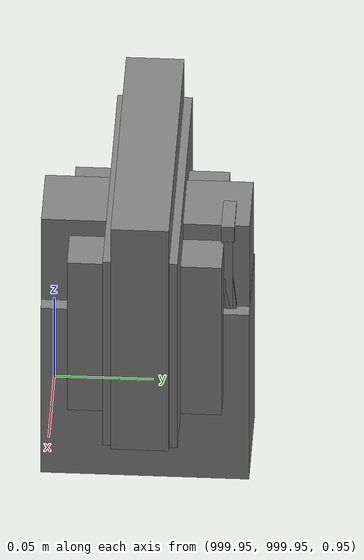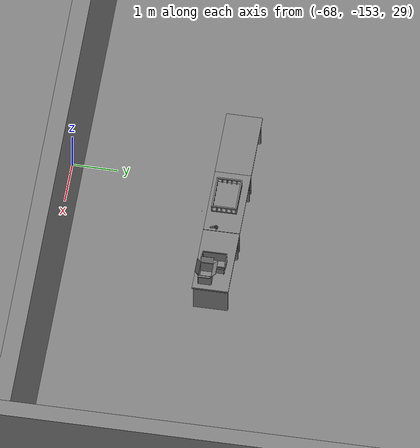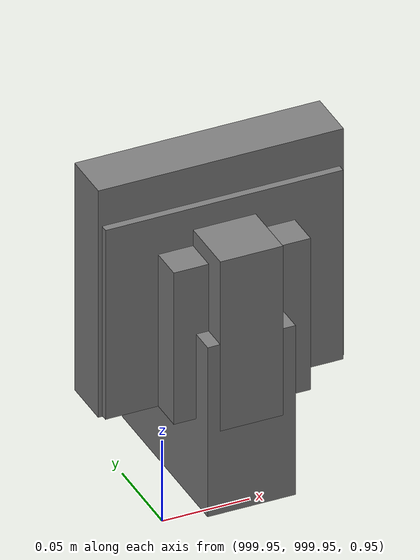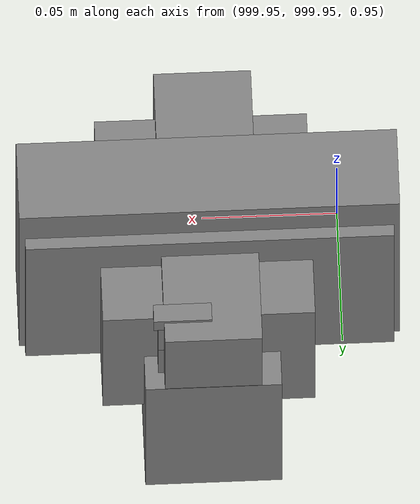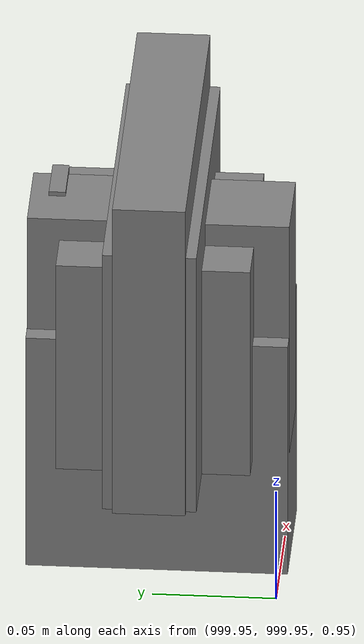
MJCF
<mujoco>
    <option gravity="0.000000000 0.000000000 -9.810000420" timestep="0.0049999999" integrator="implicitfast" density="1.225" viscosity="1.8000001e-05" noslip_iterations="10" iterations="100" sdf_iterations="50">
        <flag multiccd="disable"/>
    </option>
    <size memory="1000M"/>
    <compiler coordinate="local"/>
    <worldbody>
        <light cutoff="30" pos="0 1 1" dir="0 -1 -2"/>
        <light cutoff="30" pos="0 -1 1" dir="0 1 -2"/>
        <body pos="1000.000000000 1000.000000000 1.000000000" euler="0.000000000 0.000000000 180.000000000" name="openloong_gripper_2f85_fix_base_usda_cpu_fan">
            <geom contype="1" conaffinity="1" density="1000" type="box" material="" rgba="0.500000000 0.500000000 0.500000000 1.000000000" solimp="0.899999976 0.949999988 0.001000000" friction="1.000000000 0.005000000 0.000100000" solref="0.020000000 1.000000000" margin="0" condim="3" group="0" pos="0.000000000 0.000000000 0.070034981" quat="0.000000000 0.000000000 0.000000000 1.000000000" size="0.070700005 0.014699999 0.070700005" name="openloong_gripper_2f85_fix_base_usda_geom_E75980EF_2311_479F_8F9E_781333F5FCB8"/>
            <freejoint name="openloong_gripper_2f85_fix_base_usda_cpu_fan_joint"/>
            <site size="0.005000000 0.005000000 0.005000000" rgba="0.500000000 0.500000000 0.500000000 1.000000000" pos="0.000000000 0.000000000 0.000000000" quat="0.999961913 0.008726535 0.000000000 0.000000000" group="0" type="sphere" name="openloong_gripper_2f85_fix_base_usda_cpu_fancsite"/>
        </body>
        <body pos="1000.000000000 1000.000000000 1.000000000" euler="0.000000000 0.000000000 180.000000000" name="openloong_gripper_2f85_fix_base_usda_wifi_box">
            <geom contype="1" conaffinity="1" density="1000" type="box" material="" rgba="0.500000000 0.500000000 0.500000000 1.000000000" solimp="0.899999976 0.949999988 0.001000000" friction="1.000000000 0.005000000 0.000100000" solref="0.020000000 1.000000000" margin="0" condim="3" group="0" pos="0.000000000 0.000000000 0.058978677" quat="0.000000000 0.000000047 0.000000000 1.000000000" size="0.068499997 0.018999999 0.059000000" name="openloong_gripper_2f85_fix_base_usda_geom_D17EBFA8_A976_4396_A59F_55DAA9FCDEA4"/>
            <freejoint name="openloong_gripper_2f85_fix_base_usda_wifi_box_joint"/>
            <site size="0.005000000 0.005000000 0.005000000" rgba="0.500000000 0.500000000 0.500000000 1.000000000" pos="0.000000000 0.000000000 0.000000000" quat="0.999961913 0.008726500 0.000000000 0.000000000" group="0" type="sphere" name="openloong_gripper_2f85_fix_base_usda_wifi_boxsite"/>
        </body>
        <body pos="1000.000000000 1000.000000000 1.000000000" euler="0.000011953 0.000005123 -179.999984741" name="openloong_gripper_2f85_fix_base_usda_intel_box">
            <geom contype="1" conaffinity="1" density="1000" type="box" material="" rgba="0.500000000 0.500000000 0.500000000 1.000000000" solimp="0.899999976 0.949999988 0.001000000" friction="1.000000000 0.005000000 0.000100000" solref="0.020000000 1.000000000" margin="0" condim="3" group="0" pos="0.000000000 -0.000067139 0.000082284" quat="0.707106709 0.000000225 0.000000253 0.707106650" size="0.052800003 0.025300000 0.052800003" name="openloong_gripper_2f85_fix_base_usda_geom_D93107AE_5C60_43D9_9DDA_2C6F7B8EAFD1"/>
            <freejoint name="openloong_gripper_2f85_fix_base_usda_intel_box_joint"/>
            <site size="0.005000000 0.005000000 0.005000000" rgba="0.500000000 0.500000000 0.500000000 1.000000000" pos="0.000000000 0.000000000 0.000000000" quat="0.999961913 0.008726500 0.000000000 0.000000000" group="0" type="sphere" name="openloong_gripper_2f85_fix_base_usda_intel_boxsite"/>
        </body>
        <body pos="-65.839653015 -149.017898560 31.166585922" euler="-56.638172150 73.052680969 -45.723186493" mocap="true" name="spotlight1_SpotLight"/>
        <body pos="-66.178924561 -149.037429810 31.165462494" euler="7.649933338 -54.255420685 -119.615814209" mocap="true" name="spotlight5_SpotLight"/>
        <body pos="1000.000000000 999.999938965 1.000000000" euler="0.000000000 0.000000000 180.000000000" name="openloong_gripper_2f85_fix_base_usda_intelcore_i5">
            <geom contype="1" conaffinity="1" density="1000" type="box" material="" rgba="0.500000000 0.500000000 0.500000000 1.000000000" solimp="0.899999976 0.949999988 0.001000000" friction="1.000000000 0.005000000 0.000100000" solref="0.020000000 1.000000000" margin="0" condim="3" group="0" pos="0.000000000 0.000000000 0.051722717" quat="0.707106709 0.000000000 0.000000000 -0.707106769" size="0.052800000 0.018080002 0.052800000" name="openloong_gripper_2f85_fix_base_usda_geom_E4E93E92_2E9B_4020_9977_5BDA1FFFA879"/>
            <freejoint name="openloong_gripper_2f85_fix_base_usda_intelcore_i5_joint"/>
            <site size="0.005000000 0.005000000 0.005000000" rgba="0.500000000 0.500000000 0.500000000 1.000000000" pos="0.000000000 0.000000000 0.000000000" quat="0.999961913 0.008726534 0.000000000 0.000000000" group="0" type="sphere" name="openloong_gripper_2f85_fix_base_usda_intelcore_i5site"/>
        </body>
        <body pos="1000.000000000 1000.000000000 1.000000000" euler="0.000000000 0.000000000 180.000000000" name="openloong_gripper_2f85_fix_base_usda_battery_01">
            <geom contype="1" conaffinity="1" density="1000" type="box" material="" rgba="0.500000000 0.500000000 0.500000000 1.000000000" solimp="0.899999976 0.949999988 0.001000000" friction="1.000000000 0.005000000 0.000100000" solref="0.020000000 1.000000000" margin="0" condim="3" group="0" pos="-0.011123657 -0.041940309 0.101691343" quat="1.000000000 0.000000000 0.000000000 0.000000000" size="0.010800000 0.003375000 0.004725000" name="openloong_gripper_2f85_fix_base_usda_geom_0C1849CA_9F6F_400B_A8A2_667E811D71AF"/>
            <geom contype="1" conaffinity="1" density="1000" type="box" material="" rgba="0.500000000 0.500000000 0.500000000 1.000000000" solimp="0.899999976 0.949999988 0.001000000" friction="1.000000000 0.005000000 0.000100000" solref="0.020000000 1.000000000" margin="0" condim="3" group="0" pos="-0.010876465 -0.044247437 0.047066893" quat="0.998702705 -0.050920475 0.000000000 0.000000000" size="0.009450001 0.002700000 0.024975000" name="openloong_gripper_2f85_fix_base_usda_geom_554D70D2_C4D0_4619_8099_842EA6288B31"/>
            <geom contype="1" conaffinity="1" density="1000" type="box" material="" rgba="0.500000000 0.500000000 0.500000000 1.000000000" solimp="0.899999976 0.949999988 0.001000000" friction="1.000000000 0.005000000 0.000100000" solref="0.020000000 1.000000000" margin="0" condim="3" group="0" pos="-0.001235962 -0.000659180 0.047381196" quat="1.000000000 0.000000000 0.000000000 0.000000000" size="0.039420001 0.039150000 0.047250003" name="openloong_gripper_2f85_fix_base_usda_geom_0F6045D8_274C_40FD_8F48_E7F539551261"/>
            <geom contype="1" conaffinity="1" density="1000" type="box" material="" rgba="0.500000000 0.500000000 0.500000000 1.000000000" solimp="0.899999976 0.949999988 0.001000000" friction="1.000000000 0.005000000 0.000100000" solref="0.020000000 1.000000000" margin="0" condim="3" group="0" pos="-0.010876465 -0.039138794 0.009851727" quat="1.000000000 0.000000000 0.000000000 0.000000000" size="0.009450001 0.010800000 0.013500000" name="openloong_gripper_2f85_fix_base_usda_geom_8C85916F_ACA4_4A80_83A8_C50D816CA6C5"/>
            <geom contype="1" conaffinity="1" density="1000" type="box" material="" rgba="0.500000000 0.500000000 0.500000000 1.000000000" solimp="0.899999976 0.949999988 0.001000000" friction="1.000000000 0.005000000 0.000100000" solref="0.020000000 1.000000000" margin="0" condim="3" group="0" pos="-0.010876465 -0.041528322 0.071508206" quat="1.000000000 0.000000000 0.000000000 0.000000000" size="0.009450001 0.002700000 0.027000001" name="openloong_gripper_2f85_fix_base_usda_geom_7348D5BC_8B64_4057_8744_2BB84FA3FC1F"/>
            <freejoint name="openloong_gripper_2f85_fix_base_usda_battery_01_joint"/>
            <site size="0.005000000 0.005000000 0.005000000" rgba="0.500000000 0.500000000 0.500000000 1.000000000" pos="0.000000000 0.000000000 0.000000000" quat="0.999961913 0.008726500 0.000000000 0.000000000" group="0" type="sphere" name="openloong_gripper_2f85_fix_base_usda_battery_01site"/>
        </body>
        <body pos="-65.830154419 -149.565536499 31.167366028" euler="-121.014610291 7.475090981 -71.120040894" mocap="true" name="spotlight4_SpotLight"/>
        <body pos="-64.866622925 -149.383972168 30.183746338" euler="89.999984741 89.999946594 0.000000000" name="openloong_gripper_2f85_fix_base_usda_bluebox_01">
            <geom contype="1" conaffinity="1" density="1000" type="box" material="" rgba="0.500000000 0.500000000 0.500000000 1.000000000" solimp="0.899999976 0.949999988 0.001000000" friction="1.000000000 0.005000000 0.000100000" solref="0.020000000 1.000000000" margin="0" condim="3" group="0" pos="0.276580811 0.187225342 0.000068665" quat="0.707106948 0.000077471 0.707106352 0.000077486" size="0.100000001 0.057999998 0.010000000" name="openloong_gripper_2f85_fix_base_usda_geom_E263D736_65C5_4D6D_B54D_095C377A0984"/>
            <geom contype="1" conaffinity="1" density="1000" type="box" material="" rgba="0.500000000 0.500000000 0.500000000 1.000000000" solimp="0.899999976 0.949999988 0.001000000" friction="1.000000000 0.005000000 0.000100000" solref="0.020000000 1.000000000" margin="0" condim="3" group="0" pos="0.000000000 0.002883911 0.000000000" quat="0.999999881 0.000000000 0.000000000 0.000000000" size="0.254000008 0.003000000 0.172000006" name="openloong_gripper_2f85_fix_base_usda_geom_5929A5D1_396E_493C_A52A_D2934247FAAB"/>
            <geom contype="1" conaffinity="1" density="1000" type="box" material="" rgba="0.500000000 0.500000000 0.500000000 1.000000000" solimp="0.899999976 0.949999988 0.001000000" friction="1.000000000 0.005000000 0.000100000" solref="0.020000000 1.000000000" margin="0" condim="3" group="0" pos="0.000000000 0.124874115 0.173484802" quat="0.999796331 0.020176515 -0.000000015 0.000000030" size="0.259999990 0.119999997 0.007000000" name="openloong_gripper_2f85_fix_base_usda_geom_5D220B3F_56BF_4652_AD13_4F6F12037C8F"/>
            <geom contype="1" conaffinity="1" density="1000" type="box" material="" rgba="0.500000000 0.500000000 0.500000000 1.000000000" solimp="0.899999976 0.949999988 0.001000000" friction="1.000000000 0.005000000 0.000100000" solref="0.020000000 1.000000000" margin="0" condim="3" group="0" pos="0.000000000 0.124874115 -0.173469543" quat="0.999796331 -0.020176545 -0.000000015 0.000000000" size="0.259999990 0.119999997 0.007000000" name="openloong_gripper_2f85_fix_base_usda_geom_43C7624A_99BA_40C8_BBF2_D886E4E56E48"/>
            <geom contype="1" conaffinity="1" density="1000" type="box" material="" rgba="0.500000000 0.500000000 0.500000000 1.000000000" solimp="0.899999976 0.949999988 0.001000000" friction="1.000000000 0.005000000 0.000100000" solref="0.020000000 1.000000000" margin="0" condim="3" group="0" pos="0.000000000 0.214008331 0.188980103" quat="0.999912977 0.013176724 0.000000015 0.000000000" size="0.259999990 0.029999999 0.012500000" name="openloong_gripper_2f85_fix_base_usda_geom_B6A0F944_73B9_4DEA_A2AD_B979D7CC4EDC"/>
            <geom contype="1" conaffinity="1" density="1000" type="box" material="" rgba="0.500000000 0.500000000 0.500000000 1.000000000" solimp="0.899999976 0.949999988 0.001000000" friction="1.000000000 0.005000000 0.000100000" solref="0.020000000 1.000000000" margin="0" condim="3" group="0" pos="-0.258361816 0.125289917 0.001876831" quat="0.702796936 -0.020792112 0.710783124 0.020769298" size="0.189999998 0.119999997 0.009000000" name="openloong_gripper_2f85_fix_base_usda_geom_1E8560B0_8569_401F_884F_7860AD23932C"/>
            <geom contype="1" conaffinity="1" density="1000" type="box" material="" rgba="0.500000000 0.500000000 0.500000000 1.000000000" solimp="0.899999976 0.949999988 0.001000000" friction="1.000000000 0.005000000 0.000100000" solref="0.020000000 1.000000000" margin="0" condim="3" group="0" pos="0.000000000 0.214008331 -0.188980103" quat="0.999912977 -0.013176769 0.000000030 0.000000015" size="0.259999990 0.029999999 0.012500000" name="openloong_gripper_2f85_fix_base_usda_geom_2F826EAE_FD0B_4F0B_AB64_5B6D2BEBD07B"/>
            <geom contype="1" conaffinity="1" density="1000" type="box" material="" rgba="0.500000000 0.500000000 0.500000000 1.000000000" solimp="0.899999976 0.949999988 0.001000000" friction="1.000000000 0.005000000 0.000100000" solref="0.020000000 1.000000000" margin="0" condim="3" group="0" pos="-0.276611328 0.187225342 0.000068665" quat="0.707106650 0.000077441 0.707106709 0.000077456" size="0.100000001 0.057999998 0.010000000" name="openloong_gripper_2f85_fix_base_usda_geom_7C7EAA49_5CC8_447A_B2C8_FDDC464D4B6D"/>
            <geom contype="1" conaffinity="1" density="1000" type="box" material="" rgba="0.500000000 0.500000000 0.500000000 1.000000000" solimp="0.899999976 0.949999988 0.001000000" friction="1.000000000 0.005000000 0.000100000" solref="0.020000000 1.000000000" margin="0" condim="3" group="0" pos="0.258331299 0.125289917 0.001876831" quat="0.702851415 0.018856421 0.710823774 -0.019329369" size="0.189999998 0.119999997 0.009000000" name="openloong_gripper_2f85_fix_base_usda_geom_734EEE83_72E0_409C_B143_7F826B5100BB"/>
            <freejoint name="openloong_gripper_2f85_fix_base_usda_bluebox_01_joint"/>
            <site size="0.005000000 0.005000000 0.005000000" rgba="0.500000000 0.500000000 0.500000000 1.000000000" pos="0.000000000 0.000000000 0.000000000" quat="0.999961913 0.008726534 0.000000000 0.000000000" group="0" type="sphere" name="openloong_gripper_2f85_fix_base_usda_bluebox_01site"/>
        </body>
        <body pos="-64.496299744 -149.491867065 30.235729218" euler="0.000000000 0.000000000 89.999946594" name="openloong_gripper_2f85_fix_base_usda_cardboardbox_01">
            <geom contype="1" conaffinity="1" density="1000" type="box" material="" rgba="0.500000000 0.500000000 0.500000000 1.000000000" solimp="0.899999976 0.949999988 0.001000000" friction="1.000000000 0.005000000 0.000100000" solref="0.020000000 1.000000000" margin="0" condim="3" group="0" pos="-0.003166199 -0.004086494 0.005052090" quat="1.000000000 0.000000000 0.000000000 0.000000000" size="0.142499998 0.177500010 0.005000000" name="openloong_gripper_2f85_fix_base_usda_geom_AD20EA48_65C0_4CB8_89F1_5CAA3676F630"/>
            <geom contype="1" conaffinity="1" density="1000" type="box" material="" rgba="0.500000000 0.500000000 0.500000000 1.000000000" solimp="0.899999976 0.949999988 0.001000000" friction="1.000000000 0.005000000 0.000100000" solref="0.020000000 1.000000000" margin="0" condim="3" group="0" pos="-0.003166199 0.170316696 0.150570869" quat="1.000000000 0.000000000 0.000000000 0.000000000" size="0.142499998 0.005000000 0.149999991" name="openloong_gripper_2f85_fix_base_usda_geom_0C24CAA5_C079_4C99_AC3E_DFC906C8260E"/>
            <geom contype="1" conaffinity="1" density="1000" type="box" material="" rgba="0.500000000 0.500000000 0.500000000 1.000000000" solimp="0.899999976 0.949999988 0.001000000" friction="1.000000000 0.005000000 0.000100000" solref="0.020000000 1.000000000" margin="0" condim="3" group="0" pos="-0.147399902 -0.005307198 0.150570869" quat="1.000000000 0.000000000 0.000000000 0.000000000" size="0.005000000 0.177500010 0.149999991" name="openloong_gripper_2f85_fix_base_usda_geom_F0239B98_14AA_4659_B203_DC2AF79737F0"/>
            <geom contype="1" conaffinity="1" density="1000" type="box" material="" rgba="0.500000000 0.500000000 0.500000000 1.000000000" solimp="0.899999976 0.949999988 0.001000000" friction="1.000000000 0.005000000 0.000100000" solref="0.020000000 1.000000000" margin="0" condim="3" group="0" pos="0.140275955 -0.005307198 0.150570869" quat="1.000000000 0.000000000 0.000000000 0.000000000" size="0.005000000 0.177500010 0.149999991" name="openloong_gripper_2f85_fix_base_usda_geom_E3E389B4_20F9_4AF9_9305_7643439A935E"/>
            <geom contype="1" conaffinity="1" density="1000" type="box" material="" rgba="0.500000000 0.500000000 0.500000000 1.000000000" solimp="0.899999976 0.949999988 0.001000000" friction="1.000000000 0.005000000 0.000100000" solref="0.020000000 1.000000000" margin="0" condim="3" group="0" pos="-0.003166199 -0.181550980 0.150570869" quat="1.000000000 0.000000000 0.000000000 0.000000000" size="0.142499998 0.005000000 0.149999991" name="openloong_gripper_2f85_fix_base_usda_geom_45A59ACF_4250_45A9_9C2B_6E65A89D87A8"/>
            <freejoint name="openloong_gripper_2f85_fix_base_usda_cardboardbox_01_joint"/>
            <site size="0.005000000 0.005000000 0.005000000" rgba="0.500000000 0.500000000 0.500000000 1.000000000" pos="0.000000000 0.000000000 0.000000000" quat="0.999961913 0.008726535 0.000000000 0.000000000" group="0" type="sphere" name="openloong_gripper_2f85_fix_base_usda_site_F0D98D31_C4DE_4E1E_8E80_4BA0E499946F"/>
            <body pos="0.139160156 -0.004048347 0.301930904" euler="-179.999954224 49.383502960 179.999954224" name="openloong_gripper_2f85_fix_base_usda_A1_006">
                <geom contype="1" conaffinity="1" density="1000" type="box" material="" rgba="0.500000000 0.500000000 0.500000000 1.000000000" solimp="0.899999976 0.949999988 0.001000000" friction="1.000000000 0.005000000 0.000100000" solref="0.020000000 1.000000000" margin="0" condim="3" group="0" pos="-0.071587563 0.000009537 0.001745224" quat="0.999999881 0.000000000 0.000000000 0.000000000" size="0.071249999 0.179999992 0.002500000" name="openloong_gripper_2f85_fix_base_usda_geom_7868C7C6_001B_4F2D_BEFF_DE51D5D0C88F"/>
                <joint armature="0" stiffness="0.07" damping="0.0099999998" axis="0.000000 1.000000 0.000000" type="hinge" name="openloong_gripper_2f85_fix_base_usda_A1_006"/>
            </body>
            <body pos="-0.145902634 -0.004086494 0.301938057" euler="-180.000000000 -60.000011444 -180.000000000" name="openloong_gripper_2f85_fix_base_usda_A2_006">
                <geom contype="1" conaffinity="1" density="1000" type="box" material="" rgba="0.500000000 0.500000000 0.500000000 1.000000000" solimp="0.899999976 0.949999988 0.001000000" friction="1.000000000 0.005000000 0.000100000" solref="0.020000000 1.000000000" margin="0" condim="3" group="0" pos="0.071268082 0.000009537 0.002717972" quat="0.000002921 0.000000000 -0.000000030 0.999999881" size="0.071249999 0.179999992 0.002500000" name="openloong_gripper_2f85_fix_base_usda_geom_EB55DDF0_8937_4CCA_B0B7_8E7DC500F9AD"/>
                <joint armature="0" stiffness="0.07" damping="0.0099999998" axis="0.000000 1.000000 0.000000" type="hinge" name="openloong_gripper_2f85_fix_base_usda_A2_006"/>
            </body>
            <body pos="-0.003385544 0.175991058 0.301930904" euler="-125.858116150 -0.000004561 0.000002331" name="openloong_gripper_2f85_fix_base_usda_B2_006">
                <geom contype="1" conaffinity="1" density="1000" type="box" material="" rgba="0.500000000 0.500000000 0.500000000 1.000000000" solimp="0.899999976 0.949999988 0.001000000" friction="1.000000000 0.005000000 0.000100000" solref="0.020000000 1.000000000" margin="0" condim="3" group="0" pos="0.000009537 -0.070939064 -0.002470016" quat="0.999614120 0.027776197 -0.000000015 0.000000030" size="0.137500003 0.064999998 0.005000000" name="openloong_gripper_2f85_fix_base_usda_geom_D1BC876F_7249_4D39_8AD4_1FE03118DEDB"/>
                <joint armature="0" stiffness="0.07" damping="0.0099999998" axis="1.000000 0.000000 0.000000" type="hinge" name="openloong_gripper_2f85_fix_base_usda_B2_006"/>
            </body>
            <body pos="-0.003385544 -0.184140205 0.301938057" euler="147.805557251 0.000000000 0.000000000" name="openloong_gripper_2f85_fix_base_usda_B1_006">
                <geom contype="1" conaffinity="1" density="1000" type="box" material="" rgba="0.500000000 0.500000000 0.500000000 1.000000000" solimp="0.899999976 0.949999988 0.001000000" friction="1.000000000 0.005000000 0.000100000" solref="0.020000000 1.000000000" margin="0" condim="3" group="0" pos="-0.000028610 0.070202351 -0.002703667" quat="0.999614179 -0.027776167 0.000000000 0.000000000" size="0.137500003 0.064999998 0.005000000" name="openloong_gripper_2f85_fix_base_usda_geom_629BC5E5_E524_4E16_9701_D66EAF4D28FF"/>
                <joint armature="0" stiffness="0.07" damping="0.0099999998" axis="1.000000 0.000000 0.000000" type="hinge" name="openloong_gripper_2f85_fix_base_usda_B1_006"/>
            </body>
        </body>
        <body pos="-65.882858276 -149.481979370 30.229999542" euler="-64.487716675 0.000000000 0.000000000" name="openloong_gripper_2f85_fix_base_usda_Barcode">
            <geom contype="1" conaffinity="1" density="1000" type="box" material="" rgba="0.500000000 0.500000000 0.500000000 1.000000000" solimp="0.899999976 0.949999988 0.001000000" friction="1.000000000 0.005000000 0.000100000" solref="0.020000000 1.000000000" margin="0" condim="3" group="0" pos="0.000000000 0.013038635 0.001419067" quat="0.000000000 0.000000000 0.000000000 1.000000119" size="0.034000002 0.010000000 0.017999999" name="openloong_gripper_2f85_fix_base_usda_geom_461DE2E7_464E_4702_BC83_1A6EB8E61286"/>
            <geom contype="1" conaffinity="1" density="1000" type="box" material="" rgba="0.500000000 0.500000000 0.500000000 1.000000000" solimp="0.899999976 0.949999988 0.001000000" friction="1.000000000 0.005000000 0.000100000" solref="0.020000000 1.000000000" margin="0" condim="3" group="0" pos="0.000000000 -0.035301208 -0.007095337" quat="0.000000000 0.000000000 -0.043619365 0.999048233" size="0.028999999 0.010000000 0.020000000" name="openloong_gripper_2f85_fix_base_usda_geom_D741420C_08A6_4357_9874_3AF68587D8C4"/>
            <geom contype="1" conaffinity="1" density="1000" type="box" material="" rgba="0.500000000 0.500000000 0.500000000 1.000000000" solimp="0.899999976 0.949999988 0.001000000" friction="1.000000000 0.005000000 0.000100000" solref="0.020000000 1.000000000" margin="0" condim="3" group="0" pos="0.000000000 -0.043411255 -0.011749268" quat="0.922262907 0.386563420 0.000000000 0.000000000" size="0.026000001 0.010000000 0.020000000" name="openloong_gripper_2f85_fix_base_usda_geom_068FD8B0_9274_4F8A_A7D9_6F5E691E53E0"/>
            <geom contype="1" conaffinity="1" density="1000" type="box" material="" rgba="0.500000000 0.500000000 0.500000000 1.000000000" solimp="0.899999976 0.949999988 0.001000000" friction="1.000000000 0.005000000 0.000100000" solref="0.020000000 1.000000000" margin="0" condim="3" group="0" pos="0.000000000 -0.016967773 -0.031860352" quat="0.000000000 0.000000000 0.000000000 1.000000119" size="0.008000000 0.010000000 0.013000000" name="openloong_gripper_2f85_fix_base_usda_geom_64A3738D_F7F7_4B0F_B9CF_736F928FDF87"/>
            <geom contype="1" conaffinity="1" density="1000" type="box" material="" rgba="0.500000000 0.500000000 0.500000000 1.000000000" solimp="0.899999976 0.949999988 0.001000000" friction="1.000000000 0.005000000 0.000100000" solref="0.020000000 1.000000000" margin="0" condim="3" group="0" pos="0.000000000 -0.001869202 0.000312805" quat="0.953716993 0.300705761 0.000000000 0.000000000" size="0.032000002 0.010000000 0.018999999" name="openloong_gripper_2f85_fix_base_usda_geom_FCF2E7AD_EB38_484C_AC5E_95DE13405DEF"/>
            <geom contype="1" conaffinity="1" density="1000" type="box" material="" rgba="0.500000000 0.500000000 0.500000000 1.000000000" solimp="0.899999976 0.949999988 0.001000000" friction="1.000000000 0.005000000 0.000100000" solref="0.020000000 1.000000000" margin="0" condim="3" group="0" pos="0.000000000 -0.019531250 -0.003173828" quat="0.953716993 0.300705761 0.000000000 0.000000000" size="0.030999999 0.010000000 0.020000000" name="openloong_gripper_2f85_fix_base_usda_geom_49C3D4C8_99AD_4218_A7E2_247C83E08B30"/>
            <geom contype="1" conaffinity="1" density="1000" type="box" material="" rgba="0.500000000 0.500000000 0.500000000 1.000000000" solimp="0.899999976 0.949999988 0.001000000" friction="1.000000000 0.005000000 0.000100000" solref="0.020000000 1.000000000" margin="0" condim="3" group="0" pos="0.000000000 -0.035301208 -0.007095337" quat="0.953716993 0.300705761 0.000000000 0.000000000" size="0.028999999 0.010000000 0.020000000" name="openloong_gripper_2f85_fix_base_usda_geom_71C9A9F5_936A_4F16_A82B_8E71560ABCF4"/>
            <geom contype="1" conaffinity="1" density="1000" type="box" material="" rgba="0.500000000 0.500000000 0.500000000 1.000000000" solimp="0.899999976 0.949999988 0.001000000" friction="1.000000000 0.005000000 0.000100000" solref="0.020000000 1.000000000" margin="0" condim="3" group="0" pos="0.000000000 -0.042617798 -0.071121216" quat="0.000000000 0.000000000 0.000000000 1.000000119" size="0.013000000 0.021000000 0.059999999" name="openloong_gripper_2f85_fix_base_usda_geom_DA828D71_7BC8_4A64_8478_30CBF2E15535"/>
            <freejoint name="openloong_gripper_2f85_fix_base_usda_Barcode_joint"/>
            <site size="0.005000000 0.005000000 0.005000000" rgba="0.500000000 0.500000000 0.500000000 1.000000000" pos="0.000000000 0.000000000 0.000000000" quat="1.000000000 0.000000000 0.000000000 0.000000000" group="0" type="sphere" name="openloong_gripper_2f85_fix_base_usda_Barcode_site"/>
        </body>
        <body pos="-66.745018005 -149.392349243 30.184000015" euler="0.000000000 0.000000000 89.999946594" name="[22330787525584]_Basket_01">
            <geom contype="1" conaffinity="1" density="1000" type="box" material="" rgba="0.500000000 0.500000000 0.500000000 1.000000000" solimp="0.899999976 0.949999988 0.001000000" friction="1.000000000 0.005000000 0.000100000" solref="0.020000000 1.000000000" margin="0" condim="3" group="0" pos="-0.052425385 0.389207840 0.089787483" quat="0.707107008 0.000000000 0.000000000 0.707106411" size="0.014249999 0.014249999 0.059999999" name="[22330787525584]_geom_28370A45_7506_4266_A9B9_9F35AAB5FD4A"/>
            <geom contype="1" conaffinity="1" density="1000" type="box" material="" rgba="0.500000000 0.500000000 0.500000000 1.000000000" solimp="0.899999976 0.949999988 0.001000000" friction="1.000000000 0.005000000 0.000100000" solref="0.020000000 1.000000000" margin="0" condim="3" group="0" pos="0.264015198 -0.133043289 0.089787483" quat="0.707107008 0.000000000 0.000000000 0.707106411" size="0.014249999 0.014249999 0.059999999" name="[22330787525584]_geom_B18B3777_3A03_4A20_BBA6_EB0F5A037248"/>
            <geom contype="1" conaffinity="1" density="1000" type="box" material="" rgba="0.500000000 0.500000000 0.500000000 1.000000000" solimp="0.899999976 0.949999988 0.001000000" friction="1.000000000 0.005000000 0.000100000" solref="0.020000000 1.000000000" margin="0" condim="3" group="0" pos="-0.264015198 -0.265548706 0.089793205" quat="0.707107008 0.000000000 0.000000000 0.707106411" size="0.014249999 0.014249999 0.059999999" name="[22330787525584]_geom_2D9A5742_8A40_482C_997D_C671AC80F515"/>
            <geom contype="1" conaffinity="1" density="1000" type="box" material="" rgba="0.500000000 0.500000000 0.500000000 1.000000000" solimp="0.899999976 0.949999988 0.001000000" friction="1.000000000 0.005000000 0.000100000" solref="0.020000000 1.000000000" margin="0" condim="3" group="0" pos="-0.160263062 -0.389322281 0.089793205" quat="0.707107008 0.000000000 0.000000000 0.707106411" size="0.014249999 0.014249999 0.059999999" name="[22330787525584]_geom_062CBBF0_225B_4A65_877E_A234FB770A8A"/>
            <geom contype="1" conaffinity="1" density="1000" type="box" material="" rgba="0.500000000 0.500000000 0.500000000 1.000000000" solimp="0.899999976 0.949999988 0.001000000" friction="1.000000000 0.005000000 0.000100000" solref="0.020000000 1.000000000" margin="0" condim="3" group="0" pos="0.162265778 -0.389322281 0.089787483" quat="0.707107008 0.000000000 0.000000000 0.707106411" size="0.014249999 0.014249999 0.059999999" name="[22330787525584]_geom_ECD7FC85_025D_462E_8BE1_E3B18D083BCD"/>
            <geom contype="1" conaffinity="1" density="1000" type="box" material="" rgba="0.500000000 0.500000000 0.500000000 1.000000000" solimp="0.899999976 0.949999988 0.001000000" friction="1.000000000 0.005000000 0.000100000" solref="0.020000000 1.000000000" margin="0" condim="3" group="0" pos="0.264015198 0.389207840 0.089787483" quat="0.707107008 0.000000000 0.000000000 0.707106411" size="0.014249999 0.014249999 0.059999999" name="[22330787525584]_geom_371C6478_1439_4070_963D_BDE786396A29"/>
            <geom contype="1" conaffinity="1" density="1000" type="box" material="" rgba="0.500000000 0.500000000 0.500000000 1.000000000" solimp="0.899999976 0.949999988 0.001000000" friction="1.000000000 0.005000000 0.000100000" solref="0.020000000 1.000000000" margin="0" condim="3" group="0" pos="-0.264015198 -0.133043289 0.089793205" quat="0.707107008 0.000000000 0.000000000 0.707106411" size="0.014249999 0.014249999 0.059999999" name="[22330787525584]_geom_B27FF50C_9998_4DB0_B179_A6E296951899"/>
            <geom contype="1" conaffinity="1" density="1000" type="box" material="" rgba="0.500000000 0.500000000 0.500000000 1.000000000" solimp="0.899999976 0.949999988 0.001000000" friction="1.000000000 0.005000000 0.000100000" solref="0.020000000 1.000000000" margin="0" condim="3" group="0" pos="-0.264026642 0.269256592 0.089793205" quat="0.707107008 0.000000000 0.000000000 0.707106411" size="0.014249999 0.014249999 0.059999999" name="[22330787525584]_geom_26547C05_A4A5_43D8_8749_BC25EC8F9948"/>
            <geom contype="1" conaffinity="1" density="1000" type="box" material="" rgba="0.500000000 0.500000000 0.500000000 1.000000000" solimp="0.899999976 0.949999988 0.001000000" friction="1.000000000 0.005000000 0.000100000" solref="0.020000000 1.000000000" margin="0" condim="3" group="0" pos="0.054462433 0.389207840 0.089787483" quat="0.707107008 0.000000000 0.000000000 0.707106411" size="0.014249999 0.014249999 0.059999999" name="[22330787525584]_geom_FB59AEFB_ECB7_4A14_91A3_858A25182E7F"/>
            <geom contype="1" conaffinity="1" density="1000" type="box" material="" rgba="0.500000000 0.500000000 0.500000000 1.000000000" solimp="0.899999976 0.949999988 0.001000000" friction="1.000000000 0.005000000 0.000100000" solref="0.020000000 1.000000000" margin="0" condim="3" group="0" pos="0.054462433 -0.389322281 0.089787483" quat="0.707107008 0.000000000 0.000000000 0.707106411" size="0.014249999 0.014249999 0.059999999" name="[22330787525584]_geom_F8B2964B_F4FD_4241_864B_A5CD52899BB4"/>
            <geom contype="1" conaffinity="1" density="1000" type="box" material="" rgba="0.500000000 0.500000000 0.500000000 1.000000000" solimp="0.899999976 0.949999988 0.001000000" friction="1.000000000 0.005000000 0.000100000" solref="0.020000000 1.000000000" margin="0" condim="3" group="0" pos="0.264015198 0.269256592 0.089793205" quat="0.707107008 0.000000000 0.000000000 0.707106411" size="0.014249999 0.014249999 0.059999999" name="[22330787525584]_geom_92496100_4E3F_4C3B_960E_5D96C9BEAA89"/>
            <geom contype="1" conaffinity="1" density="1000" type="box" material="" rgba="0.500000000 0.500000000 0.500000000 1.000000000" solimp="0.899999976 0.949999988 0.001000000" friction="1.000000000 0.005000000 0.000100000" solref="0.020000000 1.000000000" margin="0" condim="3" group="0" pos="0.264015198 -0.389322281 0.089787483" quat="0.707107008 0.000000000 0.000000000 0.707106411" size="0.014249999 0.014249999 0.059999999" name="[22330787525584]_geom_9DA1EDBA_B485_4580_A634_D7BB4F9A3452"/>
            <geom contype="1" conaffinity="1" density="1000" type="box" material="" rgba="0.500000000 0.500000000 0.500000000 1.000000000" solimp="0.899999976 0.949999988 0.001000000" friction="1.000000000 0.005000000 0.000100000" solref="0.020000000 1.000000000" margin="0" condim="3" group="0" pos="0.000000000 0.000000000 0.015998840" quat="0.707107008 0.000000000 0.000000000 0.707106411" size="0.403499991 0.279000014 0.015750000" name="[22330787525584]_geom_B2B2DD68_0FEC_4D53_80DA_EC997CDB280B"/>
            <geom contype="1" conaffinity="1" density="1000" type="box" material="" rgba="0.500000000 0.500000000 0.500000000 1.000000000" solimp="0.899999976 0.949999988 0.001000000" friction="1.000000000 0.005000000 0.000100000" solref="0.020000000 1.000000000" margin="0" condim="3" group="0" pos="0.000000000 -0.389476776 0.163619041" quat="0.707107008 0.000000000 0.000000000 0.707106411" size="0.015000000 0.277500004 0.015750000" name="[22330787525584]_geom_93F79905_D189_426E_8B54_56D8601BCB0A"/>
            <geom contype="1" conaffinity="1" density="1000" type="box" material="" rgba="0.500000000 0.500000000 0.500000000 1.000000000" solimp="0.899999976 0.949999988 0.001000000" friction="1.000000000 0.005000000 0.000100000" solref="0.020000000 1.000000000" margin="0" condim="3" group="0" pos="0.162265778 0.389207840 0.089787483" quat="0.707107008 0.000000000 0.000000000 0.707106411" size="0.014249999 0.014249999 0.059999999" name="[22330787525584]_geom_9DB5C026_CD66_4E99_8845_A795ED228260"/>
            <geom contype="1" conaffinity="1" density="1000" type="box" material="" rgba="0.500000000 0.500000000 0.500000000 1.000000000" solimp="0.899999976 0.949999988 0.001000000" friction="1.000000000 0.005000000 0.000100000" solref="0.020000000 1.000000000" margin="0" condim="3" group="0" pos="0.000000000 0.389471054 0.163619041" quat="0.707107008 0.000000000 0.000000000 0.707106411" size="0.015000000 0.277500004 0.015750000" name="[22330787525584]_geom_6CCBD269_6A72_423A_984C_6A97BFF0A66D"/>
            <geom contype="1" conaffinity="1" density="1000" type="box" material="" rgba="0.500000000 0.500000000 0.500000000 1.000000000" solimp="0.899999976 0.949999988 0.001000000" friction="1.000000000 0.005000000 0.000100000" solref="0.020000000 1.000000000" margin="0" condim="3" group="0" pos="-0.263511658 0.000000000 0.163619041" quat="0.707107008 0.000000000 0.000000000 0.707106411" size="0.403499991 0.015000000 0.015750000" name="[22330787525584]_geom_304EAB6F_8436_45EA_AC97_82C9DD8B2EEA"/>
            <geom contype="1" conaffinity="1" density="1000" type="box" material="" rgba="0.500000000 0.500000000 0.500000000 1.000000000" solimp="0.899999976 0.949999988 0.001000000" friction="1.000000000 0.005000000 0.000100000" solref="0.020000000 1.000000000" margin="0" condim="3" group="0" pos="-0.264015198 0.141334534 0.089793205" quat="0.707107008 0.000000000 0.000000000 0.707106411" size="0.014249999 0.014249999 0.059999999" name="[22330787525584]_geom_FD9BE52F_2F81_4A11_816E_025179F2188C"/>
            <geom contype="1" conaffinity="1" density="1000" type="box" material="" rgba="0.500000000 0.500000000 0.500000000 1.000000000" solimp="0.899999976 0.949999988 0.001000000" friction="1.000000000 0.005000000 0.000100000" solref="0.020000000 1.000000000" margin="0" condim="3" group="0" pos="0.264015198 -0.265548706 0.089787483" quat="0.707107008 0.000000000 0.000000000 0.707106411" size="0.014249999 0.014249999 0.059999999" name="[22330787525584]_geom_640E3A2D_9165_4E31_A3A2_4722D224DE8D"/>
            <geom contype="1" conaffinity="1" density="1000" type="box" material="" rgba="0.500000000 0.500000000 0.500000000 1.000000000" solimp="0.899999976 0.949999988 0.001000000" friction="1.000000000 0.005000000 0.000100000" solref="0.020000000 1.000000000" margin="0" condim="3" group="0" pos="-0.160263062 0.389207840 0.089787483" quat="0.707107008 0.000000000 0.000000000 0.707106411" size="0.014249999 0.014249999 0.059999999" name="[22330787525584]_geom_10524394_D457_4524_A172_2A40BD989C65"/>
            <geom contype="1" conaffinity="1" density="1000" type="box" material="" rgba="0.500000000 0.500000000 0.500000000 1.000000000" solimp="0.899999976 0.949999988 0.001000000" friction="1.000000000 0.005000000 0.000100000" solref="0.020000000 1.000000000" margin="0" condim="3" group="0" pos="-0.052425385 -0.389322281 0.089787483" quat="0.707107008 0.000000000 0.000000000 0.707106411" size="0.014249999 0.014249999 0.059999999" name="[22330787525584]_geom_7D696F76_EFE3_4150_805D_C67663BDBE96"/>
            <geom contype="1" conaffinity="1" density="1000" type="box" material="" rgba="0.500000000 0.500000000 0.500000000 1.000000000" solimp="0.899999976 0.949999988 0.001000000" friction="1.000000000 0.005000000 0.000100000" solref="0.020000000 1.000000000" margin="0" condim="3" group="0" pos="-0.264026642 -0.389322281 0.089793205" quat="0.707107008 0.000000000 0.000000000 0.707106411" size="0.014249999 0.014249999 0.059999999" name="[22330787525584]_geom_62CF6363_66A4_4531_B336_DF0863783B38"/>
            <geom contype="1" conaffinity="1" density="1000" type="box" material="" rgba="0.500000000 0.500000000 0.500000000 1.000000000" solimp="0.899999976 0.949999988 0.001000000" friction="1.000000000 0.005000000 0.000100000" solref="0.020000000 1.000000000" margin="0" condim="3" group="0" pos="0.264015198 0.141334534 0.089787483" quat="0.707107008 0.000000000 0.000000000 0.707106411" size="0.014249999 0.014249999 0.059999999" name="[22330787525584]_geom_DB4A0F39_F39C_45E6_87B0_A98DEA92FE14"/>
            <geom contype="1" conaffinity="1" density="1000" type="box" material="" rgba="0.500000000 0.500000000 0.500000000 1.000000000" solimp="0.899999976 0.949999988 0.001000000" friction="1.000000000 0.005000000 0.000100000" solref="0.020000000 1.000000000" margin="0" condim="3" group="0" pos="-0.264015198 0.389207840 0.089793205" quat="0.707107008 0.000000000 0.000000000 0.707106411" size="0.014249999 0.014249999 0.059999999" name="[22330787525584]_geom_1CDD5751_EB31_4CCF_A2CC_DB032F463DD2"/>
            <geom contype="1" conaffinity="1" density="1000" type="box" material="" rgba="0.500000000 0.500000000 0.500000000 1.000000000" solimp="0.899999976 0.949999988 0.001000000" friction="1.000000000 0.005000000 0.000100000" solref="0.020000000 1.000000000" margin="0" condim="3" group="0" pos="0.264015198 0.004480362 0.089787483" quat="0.707107008 0.000000000 0.000000000 0.707106411" size="0.014249999 0.014249999 0.059999999" name="[22330787525584]_geom_4BE9FA04_5C53_4796_B71E_20A5892365F9"/>
            <geom contype="1" conaffinity="1" density="1000" type="box" material="" rgba="0.500000000 0.500000000 0.500000000 1.000000000" solimp="0.899999976 0.949999988 0.001000000" friction="1.000000000 0.005000000 0.000100000" solref="0.020000000 1.000000000" margin="0" condim="3" group="0" pos="0.263694763 -0.000011444 0.163619041" quat="0.707107008 0.000000000 0.000000000 0.707106411" size="0.403499991 0.015000000 0.015750000" name="[22330787525584]_geom_E7A02730_D617_4976_B16B_EAF9F487865C"/>
            <geom contype="1" conaffinity="1" density="1000" type="box" material="" rgba="0.500000000 0.500000000 0.500000000 1.000000000" solimp="0.899999976 0.949999988 0.001000000" friction="1.000000000 0.005000000 0.000100000" solref="0.020000000 1.000000000" margin="0" condim="3" group="0" pos="-0.264015198 0.004480362 0.089793205" quat="0.707107008 0.000000000 0.000000000 0.707106411" size="0.014249999 0.014249999 0.059999999" name="[22330787525584]_geom_5F6841A2_1752_42E1_BAC1_0B95AB347CD4"/>
            <freejoint name="[22330787525584]_joint_6A615605_F95E_49C5_A42C_C8102A441009"/>
        </body>
        <body pos="0.000000000 0.000000000 0.000000000" euler="0.000000000 0.000000000 0.000000000" name="Static Objects_Static Objects">
            <geom contype="1" conaffinity="1" density="1000" type="box" material="" rgba="0.500000000 0.500000000 0.500000000 1.000000000" solimp="0.899999976 0.949999988 0.001000000" friction="1.000000000 0.005000000 0.000100000" solref="0.020000000 1.000000000" margin="0" condim="3" group="0" pos="-67.544113159 -149.365814209 29.727830887" quat="0.500000417 0.499999970 0.499999553 0.499999970" size="0.381000012 0.319999993 0.041000001" name="Static Objects_geom_8AC8047A_6EF6_4201_AD77_1F3E1A183CB2"/>
            <geom contype="1" conaffinity="1" density="1000" type="box" material="" rgba="0.500000000 0.500000000 0.500000000 1.000000000" solimp="0.899999976 0.949999988 0.001000000" friction="1.000000000 0.005000000 0.000100000" solref="0.020000000 1.000000000" margin="0" condim="3" group="0" pos="-68.239501953 -149.365814209 30.086868286" quat="0.500000417 0.499999970 0.499999553 0.499999970" size="0.370999992 0.039500002 0.745000005" name="Static Objects_geom_0DB7F2A6_099A_4EED_84C2_8EDD05A7AC20"/>
            <geom contype="1" conaffinity="1" density="1000" type="box" material="" rgba="0.500000000 0.500000000 0.500000000 1.000000000" solimp="0.899999976 0.949999988 0.001000000" friction="1.000000000 0.005000000 0.000100000" solref="0.020000000 1.000000000" margin="0" condim="3" group="0" pos="-68.239501953 -149.365814209 30.147235870" quat="0.500000417 0.499999970 0.499999553 0.499999970" size="0.400000006 0.022000000 0.800000012" name="Static Objects_geom_508CDDE9_DF3B_4D58_90BC_660AE3DE9DF0"/>
            <geom contype="1" conaffinity="1" density="1000" type="box" material="" rgba="0.500000000 0.500000000 0.500000000 1.000000000" solimp="0.899999976 0.949999988 0.001000000" friction="1.000000000 0.005000000 0.000100000" solref="0.020000000 1.000000000" margin="0" condim="3" group="0" pos="-68.934890747 -149.365814209 29.727830887" quat="0.500000417 0.499999970 0.499999553 0.499999970" size="0.381000012 0.319999993 0.041000001" name="Static Objects_geom_B4EDC104_D367_4905_B826_90176B8E72AE"/>
            <geom contype="1" conaffinity="1" density="1000" type="box" material="" rgba="0.500000000 0.500000000 0.500000000 1.000000000" solimp="0.899999976 0.949999988 0.001000000" friction="1.000000000 0.005000000 0.000100000" solref="0.020000000 1.000000000" margin="0" condim="3" group="0" pos="-68.239501953 -149.365814209 29.561563492" quat="0.500000417 0.499999970 0.499999553 0.499999970" size="0.020000000 0.022000000 0.660000026" name="Static Objects_geom_F91E3784_13EF_4586_92FC_C08508BCEADF"/>
            <geom contype="1" conaffinity="1" density="1000" type="box" material="" rgba="0.500000000 0.500000000 0.500000000 1.000000000" solimp="0.899999976 0.949999988 0.001000000" friction="1.000000000 0.005000000 0.000100000" solref="0.020000000 1.000000000" margin="0" condim="3" group="0" pos="-65.945671082 -149.365814209 29.727830887" quat="0.500000417 0.499999970 0.499999553 0.499999970" size="0.381000012 0.319999993 0.041000001" name="Static Objects_geom_73A09B5E_6C4E_464C_A12C_B0CC05201D61"/>
            <geom contype="1" conaffinity="1" density="1000" type="box" material="" rgba="0.500000000 0.500000000 0.500000000 1.000000000" solimp="0.899999976 0.949999988 0.001000000" friction="1.000000000 0.005000000 0.000100000" solref="0.020000000 1.000000000" margin="0" condim="3" group="0" pos="-66.641059875 -149.365814209 30.086868286" quat="0.500000417 0.499999970 0.499999553 0.499999970" size="0.370999992 0.039500002 0.745000005" name="Static Objects_geom_B1461BB8_DD99_4CC4_9CB2_E1E669732192"/>
            <geom contype="1" conaffinity="1" density="1000" type="box" material="" rgba="0.500000000 0.500000000 0.500000000 1.000000000" solimp="0.899999976 0.949999988 0.001000000" friction="1.000000000 0.005000000 0.000100000" solref="0.020000000 1.000000000" margin="0" condim="3" group="0" pos="-66.641059875 -149.365814209 30.147235870" quat="0.500000417 0.499999970 0.499999553 0.499999970" size="0.400000006 0.022000000 0.800000012" name="Static Objects_geom_123EE0E1_1071_450C_B6CD_6929A90F63EA"/>
            <geom contype="1" conaffinity="1" density="1000" type="box" material="" rgba="0.500000000 0.500000000 0.500000000 1.000000000" solimp="0.899999976 0.949999988 0.001000000" friction="1.000000000 0.005000000 0.000100000" solref="0.020000000 1.000000000" margin="0" condim="3" group="0" pos="-67.336448669 -149.365814209 29.727830887" quat="0.500000417 0.499999970 0.499999553 0.499999970" size="0.381000012 0.319999993 0.041000001" name="Static Objects_geom_32751D16_90A0_432D_93BC_C5A2DD5345AE"/>
            <geom contype="1" conaffinity="1" density="1000" type="box" material="" rgba="0.500000000 0.500000000 0.500000000 1.000000000" solimp="0.899999976 0.949999988 0.001000000" friction="1.000000000 0.005000000 0.000100000" solref="0.020000000 1.000000000" margin="0" condim="3" group="0" pos="-66.641059875 -149.365814209 29.561563492" quat="0.500000417 0.499999970 0.499999553 0.499999970" size="0.020000000 0.022000000 0.660000026" name="Static Objects_geom_F514EBDC_7BF0_4F03_9AEF_588828AD7FA4"/>
            <geom contype="1" conaffinity="1" density="1000" type="box" material="" rgba="0.500000000 0.500000000 0.500000000 1.000000000" solimp="0.899999976 0.949999988 0.001000000" friction="1.000000000 0.005000000 0.000100000" solref="0.020000000 1.000000000" margin="0" condim="3" group="0" pos="-64.338577271 -149.365814209 29.727830887" quat="0.500000417 0.499999970 0.499999553 0.499999970" size="0.381000012 0.319999993 0.041000001" name="Static Objects_geom_AADD93A4_CB8C_46B2_AC08_AB094FAC4CEA"/>
            <geom contype="1" conaffinity="1" density="1000" type="box" material="" rgba="0.500000000 0.500000000 0.500000000 1.000000000" solimp="0.899999976 0.949999988 0.001000000" friction="1.000000000 0.005000000 0.000100000" solref="0.020000000 1.000000000" margin="0" condim="3" group="0" pos="-65.033966064 -149.365814209 30.086868286" quat="0.500000417 0.499999970 0.499999553 0.499999970" size="0.370999992 0.039500002 0.745000005" name="Static Objects_geom_07F12A91_F0FE_4A87_B87F_875B9402A95A"/>
            <geom contype="1" conaffinity="1" density="1000" type="box" material="" rgba="0.500000000 0.500000000 0.500000000 1.000000000" solimp="0.899999976 0.949999988 0.001000000" friction="1.000000000 0.005000000 0.000100000" solref="0.020000000 1.000000000" margin="0" condim="3" group="0" pos="-65.033966064 -149.365814209 30.147235870" quat="0.500000417 0.499999970 0.499999553 0.499999970" size="0.400000006 0.022000000 0.800000012" name="Static Objects_geom_D7E9199A_1C87_43E9_BA42_7CBD2B5F7430"/>
            <geom contype="1" conaffinity="1" density="1000" type="box" material="" rgba="0.500000000 0.500000000 0.500000000 1.000000000" solimp="0.899999976 0.949999988 0.001000000" friction="1.000000000 0.005000000 0.000100000" solref="0.020000000 1.000000000" margin="0" condim="3" group="0" pos="-65.729354858 -149.365814209 29.727830887" quat="0.500000417 0.499999970 0.499999553 0.499999970" size="0.381000012 0.319999993 0.041000001" name="Static Objects_geom_65A3CBAD_D65F_4CCB_95E2_CB501AE06E38"/>
            <geom contype="1" conaffinity="1" density="1000" type="box" material="" rgba="0.500000000 0.500000000 0.500000000 1.000000000" solimp="0.899999976 0.949999988 0.001000000" friction="1.000000000 0.005000000 0.000100000" solref="0.020000000 1.000000000" margin="0" condim="3" group="0" pos="-65.033966064 -149.365814209 29.561563492" quat="0.500000417 0.499999970 0.499999553 0.499999970" size="0.020000000 0.022000000 0.660000026" name="Static Objects_geom_3CC4307F_2B99_4A57_B8A4_73B38212B9FA"/>
            <geom contype="1" conaffinity="1" density="1000" type="box" material="" rgba="0.500000000 0.500000000 0.500000000 1.000000000" solimp="0.899999976 0.949999988 0.001000000" friction="1.000000000 0.005000000 0.000100000" solref="0.020000000 1.000000000" margin="0" condim="3" group="0" pos="-61.754566193 -137.853729248 33.906845093" quat="0.707107067 0.000000000 0.000000000 0.707106471" size="0.759999990 0.759999990 4.500000000" name="Static Objects_geom_50C27862_6959_4A11_A0C6_761CB88B7266"/>
            <geom contype="1" conaffinity="1" density="1000" type="box" material="" rgba="0.500000000 0.500000000 0.500000000 1.000000000" solimp="0.899999976 0.949999988 0.001000000" friction="1.000000000 0.005000000 0.000100000" solref="0.020000000 1.000000000" margin="0" condim="3" group="0" pos="-57.511135101 -144.927108765 31.707921982" quat="1.000000000 0.000000000 0.000000000 0.000000000" size="0.200000003 8.000000000 2.299999952" name="Static Objects_geom_5F85B9DC_EC03_41C4_9164_EFADE021F545"/>
            <geom contype="1" conaffinity="1" density="1000" type="box" material="" rgba="0.500000000 0.500000000 0.500000000 1.000000000" solimp="0.899999976 0.949999988 0.001000000" friction="1.000000000 0.005000000 0.000100000" solref="0.020000000 1.000000000" margin="0" condim="3" group="0" pos="-80.517646790 -157.574050903 31.688196182" quat="0.707107067 0.000000000 0.000000000 0.707106471" size="0.600000024 0.600000024 2.299999952" name="Static Objects_geom_CBDC1DA0_A0FF_49D4_818B_7133782D9676"/>
            <geom contype="1" conaffinity="1" density="1000" type="box" material="" rgba="0.500000000 0.500000000 0.500000000 1.000000000" solimp="0.899999976 0.949999988 0.001000000" friction="1.000000000 0.005000000 0.000100000" solref="0.020000000 1.000000000" margin="0" condim="3" group="0" pos="-80.711044312 -147.414932251 31.666158676" quat="1.000000000 0.000000000 0.000000000 0.000000000" size="0.200000003 10.000000000 2.299999952" name="Static Objects_geom_B3C3DDAF_8BD0_4BA1_870D_7041A73790EC"/>
            <geom contype="1" conaffinity="1" density="1000" type="box" material="" rgba="0.500000000 0.500000000 0.500000000 1.000000000" solimp="0.899999976 0.949999988 0.001000000" friction="1.000000000 0.005000000 0.000100000" solref="0.020000000 1.000000000" margin="0" condim="3" group="0" pos="-57.687217712 -137.434692383 31.688196182" quat="0.707107067 0.000000000 0.000000000 0.707106471" size="0.600000024 0.600000024 2.299999952" name="Static Objects_geom_066714C7_A04B_4D88_9759_136173C1ECCE"/>
            <geom contype="1" conaffinity="1" density="1000" type="box" material="" rgba="0.500000000 0.500000000 0.500000000 1.000000000" solimp="0.899999976 0.949999988 0.001000000" friction="1.000000000 0.005000000 0.000100000" solref="0.020000000 1.000000000" margin="0" condim="3" group="0" pos="-69.537033081 -140.263229370 31.714921951" quat="0.707107067 0.000000000 0.000000000 0.707106471" size="0.759999990 4.500000000 2.299999952" name="Static Objects_geom_71C66BBE_321A_481C_865F_10DC6675CAAD"/>
            <geom contype="1" conaffinity="1" density="1000" type="box" material="" rgba="0.500000000 0.500000000 0.500000000 1.000000000" solimp="0.899999976 0.949999988 0.001000000" friction="1.000000000 0.005000000 0.000100000" solref="0.020000000 1.000000000" margin="0" condim="3" group="0" pos="-80.073638916 -137.853713989 33.906845093" quat="0.707107067 0.000000000 0.000000000 0.707106471" size="0.759999990 0.759999990 4.500000000" name="Static Objects_geom_E06822C4_F759_4380_974B_68680825252B"/>
            <geom contype="1" conaffinity="1" density="1000" type="box" material="" rgba="0.500000000 0.500000000 0.500000000 1.000000000" solimp="0.899999976 0.949999988 0.001000000" friction="1.000000000 0.005000000 0.000100000" solref="0.020000000 1.000000000" margin="0" condim="3" group="0" pos="-73.406707764 -155.734664917 31.707921982" quat="1.000000000 0.000000000 0.000000000 0.000000000" size="0.200000003 3.000000000 2.299999952" name="Static Objects_geom_2D57663C_9D63_47BA_940A_35320C6B7B29"/>
            <geom contype="1" conaffinity="1" density="1000" type="box" material="" rgba="0.500000000 0.500000000 0.500000000 1.000000000" solimp="0.899999976 0.949999988 0.001000000" friction="1.000000000 0.005000000 0.000100000" solref="0.020000000 1.000000000" margin="0" condim="3" group="0" pos="-68.497543335 -137.448257446 31.707921982" quat="0.707107067 0.000000000 0.000000000 0.707106471" size="0.200000003 14.000000000 2.299999952" name="Static Objects_geom_AAA89C04_C17B_4528_8B69_875AB398EA56"/>
            <geom contype="1" conaffinity="1" density="1000" type="cylinder" material="" rgba="0.500000000 0.500000000 0.500000000 1.000000000" solimp="0.899999976 0.949999988 0.001000000" friction="1.000000000 0.005000000 0.000100000" solref="0.020000000 1.000000000" margin="0" condim="3" group="0" pos="-68.868522644 -142.134506226 31.711090088" quat="0.707107067 0.000000000 0.000000000 0.707106471" size="0.509999990 2.299999952 1.000000000" name="Static Objects_geom_365FFAAA_DC18_477C_A676_F4F588C1E0B5"/>
            <geom contype="1" conaffinity="1" density="1000" type="plane" material="" rgba="0.500000000 0.500000000 0.500000000 1.000000000" solimp="0.899999976 0.949999988 0.001000000" friction="1.000000000 0.005000000 0.000100000" solref="0.020000000 1.000000000" margin="0" condim="3" group="0" pos="-72.873703003 -147.131927490 29.409669876" quat="1.000000000 0.000000000 0.000000000 0.000000000" size="18.000000000 14.000000000 1.000000000" name="Static Objects_geom_7867CD50_322F_4005_81E4_3F6CC0F87D72"/>
            <geom contype="1" conaffinity="1" density="1000" type="box" material="" rgba="0.500000000 0.500000000 0.500000000 1.000000000" solimp="0.899999976 0.949999988 0.001000000" friction="1.000000000 0.005000000 0.000100000" solref="0.020000000 1.000000000" margin="0" condim="3" group="0" pos="-79.943580627 -157.782272339 31.707921982" quat="0.707107067 0.000000000 0.000000000 0.707106471" size="0.200000003 7.000000000 2.299999952" name="Static Objects_geom_754EFDE9_86CC_4E7B_9EA7_83FDFC16CAD6"/>
            <geom contype="1" conaffinity="1" density="1000" type="box" material="" rgba="0.500000000 0.500000000 0.500000000 1.000000000" solimp="0.899999976 0.949999988 0.001000000" friction="1.000000000 0.005000000 0.000100000" solref="0.020000000 1.000000000" margin="0" condim="3" group="0" pos="-65.421028137 -152.903442383 31.707921982" quat="0.707107067 0.000000000 0.000000000 0.707106471" size="0.200000003 7.800000191 2.299999952" name="Static Objects_geom_1BE88401_4121_4A20_A036_0C045E074919"/>
            <geom contype="1" conaffinity="1" density="1000" type="box" material="" rgba="0.500000000 0.500000000 0.500000000 1.000000000" solimp="0.899999976 0.949999988 0.001000000" friction="1.000000000 0.005000000 0.000100000" solref="0.020000000 1.000000000" margin="0" condim="3" group="0" pos="-74.776908875 -149.964416504 31.688196182" quat="1.000000000 0.000000000 0.000000000 0.000000000" size="0.600000024 0.409999996 2.299999952" name="Static Objects_geom_4CC29B8C_7C59_4408_9299_49B33C11A5EC"/>
            <geom contype="1" conaffinity="1" density="1000" type="cylinder" material="" rgba="0.500000000 0.500000000 0.500000000 1.000000000" solimp="0.899999976 0.949999988 0.001000000" friction="1.000000000 0.005000000 0.000100000" solref="0.020000000 1.000000000" margin="0" condim="3" group="0" pos="-60.161884308 -142.134506226 31.711090088" quat="0.707107067 0.000000000 0.000000000 0.707106471" size="0.509999990 2.299999952 1.000000000" name="Static Objects_geom_1283136F_B454_4872_9CC4_1485A853672F"/>
            <geom contype="1" conaffinity="1" density="1000" type="cylinder" material="" rgba="0.500000000 0.500000000 0.500000000 1.000000000" solimp="0.899999976 0.949999988 0.001000000" friction="1.000000000 0.005000000 0.000100000" solref="0.020000000 1.000000000" margin="0" condim="3" group="0" pos="-75.382453918 -149.963455200 31.711090088" quat="0.707107067 0.000000000 0.000000000 0.707106471" size="0.409999996 2.299999952 1.000000000" name="Static Objects_geom_67A496C9_2C2E_4121_9FCB_66225222AA22"/>
            <geom contype="1" conaffinity="1" density="1000" type="cylinder" material="" rgba="0.500000000 0.500000000 0.500000000 1.000000000" solimp="0.899999976 0.949999988 0.001000000" friction="1.000000000 0.005000000 0.000100000" solref="0.020000000 1.000000000" margin="0" condim="3" group="0" pos="-74.154960632 -149.963455200 31.711090088" quat="0.707107067 0.000000000 0.000000000 0.707106471" size="0.409999996 2.299999952 1.000000000" name="Static Objects_geom_60BB31DC_08D1_426A_A05A_7095D672A47B"/>
            <geom contype="1" conaffinity="1" density="1000" type="cylinder" material="" rgba="0.500000000 0.500000000 0.500000000 1.000000000" solimp="0.899999976 0.949999988 0.001000000" friction="1.000000000 0.005000000 0.000100000" solref="0.020000000 1.000000000" margin="0" condim="3" group="0" pos="-77.566612244 -142.134506226 31.711090088" quat="0.707107067 0.000000000 0.000000000 0.707106471" size="0.509999990 2.299999952 1.000000000" name="Static Objects_geom_E377DA2F_D8FD_470F_8E54_364FBF12ADEF"/>
        </body>
        <body pos="-66.291030884 -149.869689941 29.018842697" euler="0.000000000 0.000000000 89.999946594" mocap="true" name="openloong_gripper_2f85_fix_base_usda_leftHandMocap"/>
        <body pos="-66.291030884 -149.869689941 29.018842697" euler="0.000000000 0.000000000 89.999946594" mocap="true" name="openloong_gripper_2f85_fix_base_usda_rightHandMocap"/>
        <body pos="-66.291030884 -149.869689941 30.218843460" euler="0.000000000 0.000000000 89.999946594" name="openloong_gripper_2f85_fix_base_usda_base_link">
            <geom contype="1" conaffinity="1" density="1000" type="mesh" material="" rgba="0.783999979 0.783999979 0.783999979 1.000000000" solimp="0.899999976 0.949999988 0.001000000" friction="1.000000000 0.005000000 0.000100000" solref="0.020000000 1.000000000" margin="0" condim="3" group="3" mesh="base_link" pos="0.000000000 0.000000000 0.000000000" quat="1.000000000 0.000000000 0.000000000 0.000000000" size="1.000000000 1.000000000 1.000000000" name="openloong_gripper_2f85_fix_base_usda__geom_7_E04AE7ED_0BAA_4B70_83BF_127ED37940BE"/>
            <site size="0.005000000 0.005000000 0.005000000" rgba="0.500000000 0.500000000 0.500000000 1.000000000" pos="0.000000000 0.000000000 0.000000000" quat="1.000000000 0.000000000 0.000000000 0.000000000" group="0" type="sphere" name="openloong_gripper_2f85_fix_base_usda_imu"/>
            <inertial mass="22.447001" pos="-0.005664100 -0.001336700 0.238289997" diaginertia="0.374352545 0.277180195 0.220617250" quat="0.999247074 0.035235517 -0.015086859 0.006023135"/>
            <body pos="0.000000000 0.000000000 0.299997330" euler="0.000000000 0.000000000 0.000000000" name="openloong_gripper_2f85_fix_base_usda_dummy_body">
                <geom contype="1" conaffinity="1" density="1000" type="sphere" material="" rgba="0.783999979 0.783999979 0.783999979 1.000000000" solimp="0.899999976 0.949999988 0.001000000" friction="1.000000000 0.005000000 0.000100000" solref="0.020000000 1.000000000" margin="0" condim="3" group="3" pos="0.000000000 0.000000000 0.000000000" quat="1.000000000 0.000000000 0.000000000 0.000000000" size="0.010000000 0.000000000 0.000000000" name="openloong_gripper_2f85_fix_base_usda__geom_8_3E2BF136_4967_4FCD_91CF_11C2AAA5945E"/>
                <joint armature="0.0099999998" stiffness="0" damping="0.1" axis="0.000000 0.000000 1.000000" type="hinge" name="openloong_gripper_2f85_fix_base_usda_dummy_joint"/>
                <site size="0.010000000 0.005000000 0.005000000" rgba="0.500000000 0.500000000 0.500000000 1.000000000" pos="0.000000000 0.000000000 0.000000000" quat="1.000000000 0.000000000 0.000000000 0.000000000" group="3" type="sphere" name="openloong_gripper_2f85_fix_base_usda_dummy_site"/>
            </body>
            <body pos="0.009002686 0.000000000 0.406400681" euler="0.000000000 0.000000000 0.000000000" name="openloong_gripper_2f85_fix_base_usda_Link_head_yaw">
                <geom contype="1" conaffinity="1" density="1000" type="mesh" material="" rgba="0.783999979 0.783999979 0.783999979 1.000000000" solimp="0.899999976 0.949999988 0.001000000" friction="1.000000000 0.005000000 0.000100000" solref="0.020000000 1.000000000" margin="0" condim="3" group="3" mesh="Link_head_yaw" pos="0.000000000 0.000000000 0.000000000" quat="1.000000000 0.000000000 0.000000000 0.000000000" size="1.000000000 1.000000000 1.000000000" name="openloong_gripper_2f85_fix_base_usda__geom_10_1C80504B_6BFD_420B_8920_84F16C475131"/>
                <inertial mass="0.84249002" pos="0.000000000 -0.002081400 0.044801001" diaginertia="0.000700588 0.000629000 0.000553812" quat="0.706933022 -0.015675601 0.015677100 0.706933022"/>
                <body pos="0.000000000 -0.034599304 0.048500061" euler="0.000000000 0.000000000 0.000000000" name="openloong_gripper_2f85_fix_base_usda_Link_head_pitch">
                    <geom contype="1" conaffinity="1" density="1000" type="mesh" material="" rgba="0.783999979 0.783999979 0.783999979 1.000000000" solimp="0.899999976 0.949999988 0.001000000" friction="1.000000000 0.005000000 0.000100000" solref="0.020000000 1.000000000" margin="0" condim="3" group="3" mesh="Link_head_pitch" pos="0.000000000 0.000000000 0.000000000" quat="1.000000000 0.000000000 0.000000000 0.000000000" size="1.000000000 1.000000000 1.000000000" name="openloong_gripper_2f85_fix_base_usda__geom_12_693EB73E_B823_43FC_951F_5874FBE626EC"/>
                    <inertial mass="1.3943" pos="0.020569000 0.033004001 0.125000000" diaginertia="0.006381400 0.006289940 0.004481460" quat="0.973390222 0.008406822 0.228157058 0.019624906"/>
                    <body pos="0.000000000 0.029998779 0.000000000" euler="0.000000000 0.000000000 0.000000000" name="openloong_gripper_2f85_fix_base_usda_neck_center_body">
                        <site size="0.010000000 0.005000000 0.005000000" rgba="0.500000000 0.500000000 0.500000000 1.000000000" pos="0.000000000 0.000000000 0.000000000" quat="1.000000000 0.000000000 0.000000000 0.000000000" group="3" type="sphere" name="openloong_gripper_2f85_fix_base_usda_neck_center_site"/>
                        <body pos="0.020004272 0.000000000 0.149999619" euler="-0.000002229 39.998176575 -90.000205994" name="openloong_gripper_2f85_fix_base_usda_camera_head">
                            <site size="0.010000000 0.005000000 0.005000000" rgba="0.500000000 0.500000000 0.500000000 1.000000000" pos="0.000000000 0.000000000 0.000000000" quat="1.000000000 0.000000000 0.000000000 0.000000000" group="3" type="sphere" name="openloong_gripper_2f85_fix_base_usda_camera_head_site"/>
                        </body>
                    </body>
                </body>
            </body>
            <body pos="0.003997803 -0.161598206 0.392200470" euler="0.000000000 0.000000000 0.000000000" name="openloong_gripper_2f85_fix_base_usda_Link_arm_r_01">
                <geom contype="1" conaffinity="1" density="1000" type="mesh" material="" rgba="0.783999979 0.783999979 0.783999979 1.000000000" solimp="0.899999976 0.949999988 0.001000000" friction="1.000000000 0.005000000 0.000100000" solref="0.020000000 1.000000000" margin="0" condim="3" group="3" mesh="Link_arm_r_01" pos="0.000000000 0.000000000 0.000000000" quat="1.000000000 0.000000000 0.000000000 0.000000000" size="1.000000000 1.000000000 1.000000000" name="openloong_gripper_2f85_fix_base_usda__geom_14_97D01750_3815_4BE6_8F4F_04CB0238DB18"/>
                <joint armature="0.0099999998" stiffness="0" damping="1" axis="0.000000 -1.000000 0.000000" limited="true" range="-170.000015259 170.000015259" type="hinge" name="openloong_gripper_2f85_fix_base_usda_J_arm_r_01"/>
                <inertial mass="0.75641" pos="0.004494600 -0.038293999 -0.000001874" diaginertia="0.000842990 0.000803050 0.000587120" quat="-0.000163502 0.707098067 0.000812463 0.707115054"/>
                <body pos="-0.041992188 -0.041000366 0.000000000" euler="0.000000000 0.000000000 0.000000000" name="openloong_gripper_2f85_fix_base_usda_Link_arm_r_02">
                    <geom contype="1" conaffinity="1" density="1000" type="mesh" material="" rgba="0.783999979 0.783999979 0.783999979 1.000000000" solimp="0.899999976 0.949999988 0.001000000" friction="1.000000000 0.005000000 0.000100000" solref="0.020000000 1.000000000" margin="0" condim="3" group="3" mesh="Link_arm_r_02" pos="0.000000000 0.000000000 0.000000000" quat="1.000000000 0.000000000 0.000000000 0.000000000" size="1.000000000 1.000000000 1.000000000" name="openloong_gripper_2f85_fix_base_usda__geom_16_F11DDA8F_8E12_40C7_B034_AAD31B8AC660"/>
                    <joint armature="0.0099999998" stiffness="0" damping="1" axis="-1.000000 0.000000 0.000000" limited="true" range="-105.000244141 105.000244141" type="hinge" name="openloong_gripper_2f85_fix_base_usda_J_arm_r_02"/>
                    <inertial mass="0.98500001" pos="0.041999999 -0.067430697 0.000000000" diaginertia="0.002262690 0.001730990 0.001154020" quat="0.500000000 0.500000000 -0.500000000 0.500000000"/>
                    <body pos="0.041992188 -0.122596741 0.000000000" euler="0.000000000 0.000000000 0.000000000" name="openloong_gripper_2f85_fix_base_usda_Link_arm_r_03">
                        <geom contype="1" conaffinity="1" density="1000" type="mesh" material="" rgba="0.783999979 0.783999979 0.783999979 1.000000000" solimp="0.899999976 0.949999988 0.001000000" friction="1.000000000 0.005000000 0.000100000" solref="0.020000000 1.000000000" margin="0" condim="3" group="3" mesh="Link_arm_r_03" pos="0.000000000 0.000000000 0.000000000" quat="1.000000000 0.000000000 0.000000000 0.000000000" size="1.000000000 1.000000000 1.000000000" name="openloong_gripper_2f85_fix_base_usda__geom_18_83658252_0896_4C8E_A982_FB8F6EC0A0F9"/>
                        <joint armature="0.0099999998" stiffness="0" damping="1" axis="0.000000 -1.000000 0.000000" limited="true" range="-170.000015259 170.000015259" type="hinge" name="openloong_gripper_2f85_fix_base_usda_J_arm_r_03"/>
                        <inertial mass="0.95899999" pos="-0.001413580 -0.164663002 0.020757901" diaginertia="0.002101340 0.002064590 0.000754802" quat="0.560480952 0.454391927 -0.443732947 0.531497955"/>
                        <body pos="0.035293579 -0.177406311 0.023998260" euler="0.000000000 0.000000000 0.000000000" name="openloong_gripper_2f85_fix_base_usda_Link_arm_r_04">
                            <geom contype="1" conaffinity="1" density="1000" type="mesh" material="" rgba="0.783999979 0.783999979 0.783999979 1.000000000" solimp="0.899999976 0.949999988 0.001000000" friction="1.000000000 0.005000000 0.000100000" solref="0.020000000 1.000000000" margin="0" condim="3" group="3" mesh="Link_arm_r_04" pos="0.000000000 0.000000000 0.000000000" quat="1.000000000 0.000000000 0.000000000 0.000000000" size="1.000000000 1.000000000 1.000000000" name="openloong_gripper_2f85_fix_base_usda__geom_20_03ABC57F_0395_4A4D_AE7C_C0AAC096940B"/>
                            <joint armature="0.0099999998" stiffness="0" damping="1" axis="-1.000000 0.000000 0.000000" limited="true" range="0.000000000 170.000015259" type="hinge" name="openloong_gripper_2f85_fix_base_usda_J_arm_r_04"/>
                            <inertial mass="0.60000002" pos="-0.038727000 -0.060766999 -0.021003000" diaginertia="0.001092610 0.000712422 0.000645102" quat="0.327701002 0.632602990 -0.467366993 0.523443997"/>
                            <body pos="-0.035293579 -0.103492737 -0.023998260" euler="0.000000000 0.000000000 0.000000000" name="openloong_gripper_2f85_fix_base_usda_Link_arm_r_05">
                                <geom contype="1" conaffinity="1" density="1000" type="mesh" material="" rgba="0.783999979 0.783999979 0.783999979 1.000000000" solimp="0.899999976 0.949999988 0.001000000" friction="1.000000000 0.005000000 0.000100000" solref="0.020000000 1.000000000" margin="0" condim="3" group="3" mesh="Link_arm_r_05" pos="0.000000000 0.000000000 0.000000000" quat="1.000000000 0.000000000 0.000000000 0.000000000" size="1.000000000 1.000000000 1.000000000" name="openloong_gripper_2f85_fix_base_usda__geom_22_A22047D7_88CC_4240_A9B5_48DD3C221C6D"/>
                                <joint armature="0.0099999998" stiffness="0" damping="1" axis="0.000000 -1.000000 0.000000" limited="true" range="-170.000015259 170.000015259" type="hinge" name="openloong_gripper_2f85_fix_base_usda_J_arm_r_05"/>
                                <inertial mass="0.68976003" pos="0.000032712 -0.068658002 -0.000111780" diaginertia="0.002522510 0.002411100 0.000448695" quat="0.707660973 0.706543028 -0.002603360 0.002470550"/>
                                <body pos="-0.026489258 -0.196502686 0.000000000" euler="0.000000000 0.000000000 0.000000000" name="openloong_gripper_2f85_fix_base_usda_Link_arm_r_06">
                                    <geom contype="1" conaffinity="1" density="1000" type="mesh" material="" rgba="0.783999979 0.783999979 0.783999979 1.000000000" solimp="0.899999976 0.949999988 0.001000000" friction="1.000000000 0.005000000 0.000100000" solref="0.020000000 1.000000000" margin="0" condim="3" group="3" mesh="Link_arm_r_06" pos="0.000000000 0.000000000 0.000000000" quat="1.000000000 0.000000000 0.000000000 0.000000000" size="1.000000000 1.000000000 1.000000000" name="openloong_gripper_2f85_fix_base_usda__geom_24_82BBB3A8_E0BB_4FD3_BD3D_A228C4536F86"/>
                                    <joint armature="0.0099999998" stiffness="0" damping="1" axis="1.000000 0.000000 0.000000" limited="true" range="-105.000244141 105.000244141" type="hinge" name="openloong_gripper_2f85_fix_base_usda_J_arm_r_06"/>
                                    <inertial mass="0.28" pos="0.026078001 -0.000000896 0.001663700" diaginertia="0.000156930 0.000145601 0.000104979" quat="0.707080841 0.001851080 0.001883810 0.707127810"/>
                                    <body pos="0.026489258 0.000000000 0.031799316" euler="0.000000000 0.000000000 0.000000000" name="openloong_gripper_2f85_fix_base_usda_Link_arm_r_07">
                                        <geom contype="1" conaffinity="1" density="1000" type="mesh" material="" rgba="0.783999979 0.783999979 0.783999979 1.000000000" solimp="0.899999976 0.949999988 0.001000000" friction="1.000000000 0.005000000 0.000100000" solref="0.020000000 1.000000000" margin="0" condim="3" group="3" mesh="Link_arm_r_07" pos="0.000000000 0.000000000 0.000000000" quat="1.000000000 0.000000000 0.000000000 0.000000000" size="1.000000000 1.000000000 1.000000000" name="openloong_gripper_2f85_fix_base_usda__geom_26_0DC64EB8_0C6C_4EEB_84CA_C476832D3D5C"/>
                                        <joint armature="0.0099999998" stiffness="0" damping="1" axis="0.000000 0.000000 1.000000" limited="true" range="-60.000133514 60.000133514" type="hinge" name="openloong_gripper_2f85_fix_base_usda_J_arm_r_07"/>
                                        <inertial mass="0.61353999" pos="-0.007859000 -0.158170000 -0.027736001" diaginertia="0.003037610 0.002570910 0.000729379" quat="0.427542925 0.443532884 -0.553093910 0.560867906"/>
                                        <body pos="0.000000000 0.286994934 -0.270000458" euler="150.000350952 -0.000001649 -0.000000442" name="openloong_gripper_2f85_fix_base_usda_camera_wrist_r">
                                            <site size="0.010000000 0.005000000 0.005000000" rgba="0.500000000 0.500000000 0.500000000 1.000000000" pos="0.000000000 0.000000000 0.000000000" quat="1.000000000 0.000000000 0.000000000 0.000000000" group="3" type="sphere" name="openloong_gripper_2f85_fix_base_usda_camera_wrist_r_site"/>
                                        </body>
                                        <body pos="0.000000000 -0.220008850 -0.033002853" euler="0.000000000 0.000000000 179.999969482" name="openloong_gripper_2f85_fix_base_usda_ee_center_body_r">
                                            <site size="0.010000000 0.005000000 0.005000000" rgba="0.500000000 0.500000000 0.500000000 1.000000000" pos="0.000000000 0.000000000 0.000000000" quat="1.000000000 0.000000000 0.000000000 0.000000000" group="3" type="sphere" name="openloong_gripper_2f85_fix_base_usda_ee_center_site_r"/>
                                        </body>
                                        <body pos="0.000000000 -0.066001892 -0.031000137" euler="89.999984741 0.000000000 180.000000000" name="openloong_gripper_2f85_fix_base_usda_zbr_base_link">
                                            <geom contype="1" conaffinity="1" density="1000" type="mesh" material="" rgba="0.783999979 0.783999979 0.783999979 1.000000000" solimp="0.899999976 0.949999988 0.001000000" friction="1.000000000 0.005000000 0.000100000" solref="0.020000000 1.000000000" margin="0" condim="3" group="3" mesh="base" pos="0.000000000 0.000003815 -0.000007629" quat="1.000000000 0.000000000 0.000000000 0.000000000" size="1.000000238 1.000000238 1.000000238" name="openloong_gripper_2f85_fix_base_usda__geom_30_94611E09_D7C9_4E60_9FC3_C5CCF62E665C"/>
                                            <inertial mass="0.77744102" pos="0.000000000 -0.000027039 0.035467502" diaginertia="0.000260285 0.000225381 0.000152708" quat="0.999998808 -0.001528488 0.000000000 0.000000000"/>
                                            <body pos="-0.030609138 0.004745484 0.065696731" euler="-89.999984741 -0.000000000 0.000000000" name="openloong_gripper_2f85_fix_base_usda_r_left_driver">
                                                <geom contype="1" conaffinity="1" density="1000" type="mesh" material="" rgba="0.783999979 0.783999979 0.783999979 1.000000000" solimp="0.899999976 0.949999988 0.001000000" friction="1.000000000 0.005000000 0.000100000" solref="0.020000000 1.000000000" margin="0" condim="3" group="3" mesh="driver" pos="0.030609138 0.054901138 -0.004699708" quat="0.707106829 0.707106709 0.000000000 -0.000000000" size="1.000000238 1.000000238 1.000000238" name="openloong_gripper_2f85_fix_base_usda__geom_32_2CE1FBE9_26E6_4D25_9207_BE5751A5F675"/>
                                                <joint armature="0.0049999999" stiffness="0" damping="0.1" axis="0.000000 0.000000 1.000000" limited="true" range="0.000000000 51.566200256" type="hinge" name="openloong_gripper_2f85_fix_base_usda_r_left_driver_joint"/>
                                                <inertial mass="0.0089956298" pos="0.000000000 0.017754700 0.001073140" diaginertia="0.000001724 0.000001609 0.000000322" quat="0.681301236 0.732003212 0.000000000 0.000000000"/>
                                                <body pos="-0.031402595 0.004524232 -0.010200503" euler="0.000000000 0.000000000 180.000000000" name="openloong_gripper_2f85_fix_base_usda_r_left_coupler">
                                                    <geom contype="1" conaffinity="1" density="1000" type="mesh" material="" rgba="0.783999979 0.783999979 0.783999979 1.000000000" solimp="0.899999976 0.949999988 0.001000000" friction="1.000000000 0.005000000 0.000100000" solref="0.020000000 1.000000000" margin="0" condim="3" group="3" mesh="coupler" pos="-0.062011734 -0.050354015 0.005500795" quat="0.707106829 -0.707106709 0.000000000 -0.000000000" size="1.000000238 1.000000238 1.000000238" name="openloong_gripper_2f85_fix_base_usda__geom_34_C23E0D35_42AC_4829_BA73_8BC0C253E40C"/>
                                                    <inertial mass="0.0140974" pos="0.000000000 0.003012090 0.023217499" diaginertia="0.000004162 0.000003522 0.000000888" quat="0.705635548 -0.045590367 0.045590367 0.705635548"/>
                                                </body>
                                            </body>
                                            <body pos="-0.012695315 -0.012001040 0.072212234" euler="-89.999984741 -0.000000000 0.000000000" name="openloong_gripper_2f85_fix_base_usda_r_left_spring_link">
                                                <geom contype="1" conaffinity="1" density="1000" type="mesh" material="" rgba="0.783999979 0.783999979 0.783999979 1.000000000" solimp="0.899999976 0.949999988 0.001000000" friction="1.000000000 0.005000000 0.000100000" solref="0.020000000 1.000000000" margin="0" condim="3" group="3" mesh="spring_link" pos="0.012695315 0.061416641 0.012050631" quat="0.707106829 0.707106709 0.000000000 -0.000000000" size="1.000000238 1.000000238 1.000000238" name="openloong_gripper_2f85_fix_base_usda__geom_36_E4A136F4_A07A_407A_BA8A_C045DF9A955C"/>
                                                <joint armature="0.001" stiffness="0.050000001" damping="0.00125" axis="0.000000 0.000000 1.000000" limited="true" range="-17.000000000 51.566200256" type="hinge" name="openloong_gripper_2f85_fix_base_usda_r_left_spring_link_joint"/>
                                                <inertial mass="0.0221642" pos="-0.000000009 0.018162400 0.021265799" diaginertia="0.000008969 0.000006717 0.000002639" quat="0.663403213 -0.244737089 0.244737089 0.663403213"/>
                                                <body pos="-0.038208015 -0.042503368 0.002950669" euler="180.000000000 0.000000000 -0.002185660" name="openloong_gripper_2f85_fix_base_usda_r_left_follower">
                                                    <geom contype="1" conaffinity="1" density="1000" type="mesh" material="" rgba="0.783999979 0.783999979 0.783999979 1.000000000" solimp="0.899999976 0.949999988 0.001000000" friction="1.000000000 0.005000000 0.000100000" solref="0.020000000 1.000000000" margin="0" condim="3" group="3" mesh="tongue" pos="0.050918590 -0.103920005 -0.009099962" quat="0.707106829 -0.707106709 0.000000030 0.000000030" size="1.000000238 1.000000238 1.000000238" name="openloong_gripper_2f85_fix_base_usda__geom_40_5223AB7B_23DC_4489_B6D8_82DEF26A026A"/>
                                                    <geom contype="1" conaffinity="1" density="1000" type="mesh" material="" rgba="0.783999979 0.783999979 0.783999979 1.000000000" solimp="0.899999976 0.949999988 0.001000000" friction="1.000000000 0.005000000 0.000100000" solref="0.020000000 1.000000000" margin="0" condim="3" group="3" mesh="follower" pos="0.050918590 -0.103920005 -0.009099962" quat="0.707106829 -0.707106709 0.000000030 0.000000030" size="1.000000238 1.000000238 1.000000238" name="openloong_gripper_2f85_fix_base_usda__geom_39_9C0EB200_D309_4AFA_AE8B_12160769FF5C"/>
                                                    <joint armature="0.001" stiffness="0" damping="0.1" axis="0.000000 0.000000 1.000000" limited="true" range="-49.999961853 51.566200256" type="hinge" name="openloong_gripper_2f85_fix_base_usda_r_left_follower"/>
                                                    <inertial mass="0.0125222" pos="0.000000000 -0.011046000 0.012478600" diaginertia="0.000002674 0.000002456 0.000000602" quat="0.986436546 0.164143041 0.000000000 0.000000000"/>
                                                    <body pos="-0.037765510 -0.103912376 -0.009099962" euler="-89.999984741 0.000000000 0.000004829" name="openloong_gripper_2f85_fix_base_usda_r_left_pad">
                                                        <geom contype="1" conaffinity="1" density="1000" type="box" material="" rgba="0.550000012 0.550000012 0.550000012 1.000000000" solimp="0.949999988 0.990000010 0.001000000" friction="0.699999988 0.005000000 0.000100000" solref="0.020000000 1.000000000" margin="0" condim="3" group="3" mass="1e-06" pos="0.043243419 0.000003815 0.119995147" quat="0.999999881 0.000000000 0.000000000 0.000000000" size="0.002000001 0.011000003 0.009375002" name="openloong_gripper_2f85_fix_base_usda_r_left_pad1_2E7A7D72_88E7_4AAF_8972_7A2C83D5167B"/>
                                                        <geom contype="1" conaffinity="1" density="1000" type="box" material="" rgba="0.449999988 0.449999988 0.449999988 1.000000000" solimp="0.949999988 0.990000010 0.001000000" friction="0.600000024 0.005000000 0.000100000" solref="0.020000000 1.000000000" margin="0" condim="3" group="3" mass="1e-06" pos="0.043243419 0.000003815 0.138748199" quat="0.999999881 0.000000000 0.000000000 0.000000000" size="0.002000001 0.011000003 0.009375002" name="openloong_gripper_2f85_fix_base_usda_r_left_pad2_41853EAD_F3DA_484B_971C_47D532AB0597"/>
                                                    </body>
                                                </body>
                                            </body>
                                            <body pos="0.030593880 -0.004753114 0.065696731" euler="89.999984741 0.000000000 180.000000000" name="openloong_gripper_2f85_fix_base_usda_r_right_driver">
                                                <geom contype="1" conaffinity="1" density="1000" type="mesh" material="" rgba="0.783999979 0.783999979 0.783999979 1.000000000" solimp="0.899999976 0.949999988 0.001000000" friction="1.000000000 0.005000000 0.000100000" solref="0.020000000 1.000000000" margin="0" condim="3" group="3" mesh="driver" pos="0.030593880 0.054901138 -0.004699708" quat="0.707106829 0.707106709 0.000000000 0.000000000" size="1.000000238 1.000000238 1.000000238" name="openloong_gripper_2f85_fix_base_usda__geom_42_FA6AE897_AD73_46F4_930C_B16A8560935D"/>
                                                <joint armature="0.0049999999" stiffness="0" damping="0.1" axis="0.000000 0.000000 1.000000" limited="true" range="0.000000000 51.566200256" type="hinge" name="openloong_gripper_2f85_fix_base_usda_r_right_driver_joint"/>
                                                <inertial mass="0.0089956298" pos="0.000000000 0.017754700 0.001073140" diaginertia="0.000001724 0.000001609 0.000000322" quat="0.681301236 0.732003212 0.000000000 0.000000000"/>
                                                <body pos="-0.031417854 0.004531861 -0.010202411" euler="0.000000000 0.000000000 180.000000000" name="openloong_gripper_2f85_fix_base_usda_r_right_coupler">
                                                    <geom contype="1" conaffinity="1" density="1000" type="mesh" material="" rgba="0.783999979 0.783999979 0.783999979 1.000000000" solimp="0.899999976 0.949999988 0.001000000" friction="1.000000000 0.005000000 0.000100000" solref="0.020000000 1.000000000" margin="0" condim="3" group="3" mesh="coupler" pos="-0.062042251 -0.050376903 0.005500795" quat="0.707106829 -0.707106709 0.000000000 0.000000000" size="1.000000238 1.000000238 1.000000238" name="openloong_gripper_2f85_fix_base_usda__geom_44_DE355911_83DE_4150_856B_31832F22C8F1"/>
                                                    <inertial mass="0.0140974" pos="0.000000000 0.003012090 0.023217499" diaginertia="0.000004162 0.000003522 0.000000888" quat="0.705635548 -0.045590367 0.045590367 0.705635548"/>
                                                </body>
                                            </body>
                                            <body pos="0.012695315 0.011997226 0.072219864" euler="89.999984741 0.000000000 180.000000000" name="openloong_gripper_2f85_fix_base_usda_r_right_spring_link">
                                                <geom contype="1" conaffinity="1" density="1000" type="mesh" material="" rgba="0.783999979 0.783999979 0.783999979 1.000000000" solimp="0.899999976 0.949999988 0.001000000" friction="1.000000000 0.005000000 0.000100000" solref="0.020000000 1.000000000" margin="0" condim="3" group="3" mesh="spring_link" pos="0.012695315 0.061424270 0.012048724" quat="0.707106829 0.707106709 0.000000000 0.000000000" size="1.000000238 1.000000238 1.000000238" name="openloong_gripper_2f85_fix_base_usda__geom_46_3F8DBDC2_4363_4FF8_9916_E853BFEEBF94"/>
                                                <joint armature="0.001" stiffness="0.050000001" damping="0.00125" axis="0.000000 0.000000 1.000000" limited="true" range="-17.000000000 51.566200256" type="hinge" name="openloong_gripper_2f85_fix_base_usda_r_right_spring_link_joint"/>
                                                <inertial mass="0.0221642" pos="-0.000000009 0.018162400 0.021265799" diaginertia="0.000008969 0.000006717 0.000002639" quat="0.663403213 -0.244737089 0.244737089 0.663403213"/>
                                                <body pos="-0.038208015 -0.042495739 0.002950669" euler="180.000000000 0.000000000 0.000000000" name="openloong_gripper_2f85_fix_base_usda_r_right_follower">
                                                    <geom contype="1" conaffinity="1" density="1000" type="mesh" material="" rgba="0.783999979 0.783999979 0.783999979 1.000000000" solimp="0.899999976 0.949999988 0.001000000" friction="1.000000000 0.005000000 0.000100000" solref="0.020000000 1.000000000" margin="0" condim="3" group="3" mesh="follower" pos="0.050888073 -0.103927635 -0.009099962" quat="0.707106829 -0.707106709 0.000000000 0.000000000" size="1.000000238 1.000000238 1.000000238" name="openloong_gripper_2f85_fix_base_usda__geom_50_55EC87D2_9CC0_469A_906F_C956371CDEA7"/>
                                                    <geom contype="1" conaffinity="1" density="1000" type="mesh" material="" rgba="0.783999979 0.783999979 0.783999979 1.000000000" solimp="0.899999976 0.949999988 0.001000000" friction="1.000000000 0.005000000 0.000100000" solref="0.020000000 1.000000000" margin="0" condim="3" group="3" mesh="tongue" pos="0.050888073 -0.103927635 -0.009099962" quat="0.707106829 -0.707106709 0.000000000 0.000000000" size="1.000000238 1.000000238 1.000000238" name="openloong_gripper_2f85_fix_base_usda__geom_49_98C472D8_C05E_4AF5_BA80_0B4B4ED7D50F"/>
                                                    <joint armature="0.001" stiffness="0" damping="0.1" axis="0.000000 0.000000 1.000000" limited="true" range="-49.999961853 51.566200256" type="hinge" name="openloong_gripper_2f85_fix_base_usda_r_right_follower_joint"/>
                                                    <inertial mass="0.0125222" pos="0.000000000 -0.011046000 0.012478600" diaginertia="0.000002674 0.000002456 0.000000602" quat="0.986436546 0.164143041 0.000000000 0.000000000"/>
                                                    <body pos="-0.037811287 -0.103927635 -0.009099962" euler="-89.999984741 0.000000000 0.000000000" name="openloong_gripper_2f85_fix_base_usda_r_right_pad">
                                                        <geom contype="1" conaffinity="1" density="1000" type="box" material="" rgba="0.449999988 0.449999988 0.449999988 1.000000000" solimp="0.949999988 0.990000010 0.001000000" friction="0.600000024 0.005000000 0.000100000" solref="0.020000000 1.000000000" margin="0" condim="3" group="3" mass="1e-06" pos="0.043258678 0.000000000 0.138748199" quat="1.000000000 0.000000000 0.000000000 0.000000000" size="0.002000001 0.011000003 0.009375002" name="openloong_gripper_2f85_fix_base_usda_r_right_pad2_7287F9F9_6EE6_4120_A531_4CF66AB718E3"/>
                                                        <geom contype="1" conaffinity="1" density="1000" type="box" material="" rgba="0.550000012 0.550000012 0.550000012 1.000000000" solimp="0.949999988 0.990000010 0.001000000" friction="0.699999988 0.005000000 0.000100000" solref="0.020000000 1.000000000" margin="0" condim="3" group="3" mass="1e-06" pos="0.043258678 0.000003815 0.120002776" quat="1.000000000 0.000000000 0.000000000 0.000000000" size="0.002000001 0.011000003 0.009375002" name="openloong_gripper_2f85_fix_base_usda_r_right_pad1_43801D3C_E3E5_4BB2_AD22_E2DB2EEA873A"/>
                                                    </body>
                                                </body>
                                            </body>
                                        </body>
                                    </body>
                                </body>
                            </body>
                        </body>
                    </body>
                </body>
            </body>
            <body pos="0.003997803 0.161590576 0.392200470" euler="0.000000000 0.000000000 0.000000000" name="openloong_gripper_2f85_fix_base_usda_Link_arm_l_01">
                <geom contype="1" conaffinity="1" density="1000" type="mesh" material="" rgba="0.783999979 0.783999979 0.783999979 1.000000000" solimp="0.899999976 0.949999988 0.001000000" friction="1.000000000 0.005000000 0.000100000" solref="0.020000000 1.000000000" margin="0" condim="3" group="3" mesh="Link_arm_l_01" pos="0.000000000 0.000000000 0.000000000" quat="1.000000000 0.000000000 0.000000000 0.000000000" size="1.000000000 1.000000000 1.000000000" name="openloong_gripper_2f85_fix_base_usda__geom_52_E26E7D35_3A23_4E23_8575_1B6B01F27BC0"/>
                <joint armature="0.0099999998" stiffness="0" damping="1" axis="0.000000 1.000000 0.000000" limited="true" range="-170.000015259 170.000015259" type="hinge" name="openloong_gripper_2f85_fix_base_usda_J_arm_l_01"/>
                <inertial mass="0.75640601" pos="-0.004494650 0.038294200 -0.000001874" diaginertia="0.000842986 0.000803053 0.000587115" quat="-0.000812496 0.707115054 0.000163424 0.707098067"/>
                <body pos="0.042007446 0.041000366 0.000000000" euler="0.000000000 0.000000000 0.000000000" name="openloong_gripper_2f85_fix_base_usda_Link_arm_l_02">
                    <geom contype="1" conaffinity="1" density="1000" type="mesh" material="" rgba="0.783999979 0.783999979 0.783999979 1.000000000" solimp="0.899999976 0.949999988 0.001000000" friction="1.000000000 0.005000000 0.000100000" solref="0.020000000 1.000000000" margin="0" condim="3" group="3" mesh="Link_arm_l_02" pos="0.000000000 0.000000000 0.000000000" quat="1.000000000 0.000000000 0.000000000 0.000000000" size="1.000000000 1.000000000 1.000000000" name="openloong_gripper_2f85_fix_base_usda__geom_54_C6804B9F_634B_41AE_A7B2_0248B711A525"/>
                    <joint armature="0.0099999998" stiffness="0" damping="1" axis="-1.000000 0.000000 0.000000" limited="true" range="-105.000244141 105.000244141" type="hinge" name="openloong_gripper_2f85_fix_base_usda_J_arm_l_02"/>
                    <inertial mass="0.98500001" pos="-0.041999999 0.067430697 0.000000000" diaginertia="0.002262690 0.001730990 0.001154020" quat="0.500000000 0.500000000 -0.500000000 0.500000000"/>
                    <body pos="-0.042007446 0.122596741 0.000000000" euler="0.000000000 0.000000000 0.000000000" name="openloong_gripper_2f85_fix_base_usda_Link_arm_l_03">
                        <geom contype="1" conaffinity="1" density="1000" type="mesh" material="" rgba="0.783999979 0.783999979 0.783999979 1.000000000" solimp="0.899999976 0.949999988 0.001000000" friction="1.000000000 0.005000000 0.000100000" solref="0.020000000 1.000000000" margin="0" condim="3" group="3" mesh="Link_arm_l_03" pos="0.000000000 0.000000000 0.000000000" quat="1.000000000 0.000000000 0.000000000 0.000000000" size="1.000000000 1.000000000 1.000000000" name="openloong_gripper_2f85_fix_base_usda__geom_56_56E87863_0D1F_41C2_9A12_89762D7B3402"/>
                        <joint armature="0.0099999998" stiffness="0" damping="1" axis="0.000000 1.000000 0.000000" limited="true" range="-170.000015259 170.000015259" type="hinge" name="openloong_gripper_2f85_fix_base_usda_J_arm_l_03"/>
                        <inertial mass="0.95899999" pos="0.001413580 0.164663002 0.020757901" diaginertia="0.002101340 0.002064590 0.000754802" quat="0.443732947 0.531497955 -0.560480952 0.454391927"/>
                        <body pos="-0.035293579 0.177406311 0.023998260" euler="0.000000000 0.000000000 0.000000000" name="openloong_gripper_2f85_fix_base_usda_Link_arm_l_04">
                            <geom contype="1" conaffinity="1" density="1000" type="mesh" material="" rgba="0.783999979 0.783999979 0.783999979 1.000000000" solimp="0.899999976 0.949999988 0.001000000" friction="1.000000000 0.005000000 0.000100000" solref="0.020000000 1.000000000" margin="0" condim="3" group="3" mesh="Link_arm_l_04" pos="0.000000000 0.000000000 0.000000000" quat="1.000000000 0.000000000 0.000000000 0.000000000" size="1.000000000 1.000000000 1.000000000" name="openloong_gripper_2f85_fix_base_usda__geom_58_639387BE_CC2A_4786_A189_EA151DE2D66D"/>
                            <joint armature="0.0099999998" stiffness="0" damping="1" axis="1.000000 0.000000 0.000000" limited="true" range="0.000000000 170.000015259" type="hinge" name="openloong_gripper_2f85_fix_base_usda_J_arm_l_04"/>
                            <inertial mass="0.60000002" pos="0.038727000 0.060767200 -0.021003200" diaginertia="0.001092570 0.000712419 0.000645098" quat="0.467370987 0.523440003 -0.327692002 0.632607996"/>
                            <body pos="0.035293579 0.103500366 -0.023998260" euler="0.000000000 0.000000000 0.000000000" name="openloong_gripper_2f85_fix_base_usda_Link_arm_l_05">
                                <geom contype="1" conaffinity="1" density="1000" type="mesh" material="" rgba="0.783999979 0.783999979 0.783999979 1.000000000" solimp="0.899999976 0.949999988 0.001000000" friction="1.000000000 0.005000000 0.000100000" solref="0.020000000 1.000000000" margin="0" condim="3" group="3" mesh="Link_arm_l_05" pos="0.000000000 0.000000000 0.000000000" quat="1.000000000 0.000000000 0.000000000 0.000000000" size="1.000000000 1.000000000 1.000000000" name="openloong_gripper_2f85_fix_base_usda__geom_60_02BCE21F_E584_40CF_A8FB_C4D1AFD42D1A"/>
                                <joint armature="0.0099999998" stiffness="0" damping="1" axis="0.000000 1.000000 0.000000" limited="true" range="-170.000015259 170.000015259" type="hinge" name="openloong_gripper_2f85_fix_base_usda_J_arm_l_05"/>
                                <inertial mass="0.68976003" pos="-0.000032712 0.068658002 -0.000111780" diaginertia="0.002522510 0.002411100 0.000448695" quat="0.706543028 0.707660973 0.002470550 -0.002603360"/>
                                <body pos="0.026504517 0.196495056 0.000000000" euler="0.000000000 0.000000000 0.000000000" name="openloong_gripper_2f85_fix_base_usda_Link_arm_l_06">
                                    <geom contype="1" conaffinity="1" density="1000" type="mesh" material="" rgba="0.783999979 0.783999979 0.783999979 1.000000000" solimp="0.899999976 0.949999988 0.001000000" friction="1.000000000 0.005000000 0.000100000" solref="0.020000000 1.000000000" margin="0" condim="3" group="3" mesh="Link_arm_l_06" pos="0.000000000 0.000000000 0.000000000" quat="1.000000000 0.000000000 0.000000000 0.000000000" size="1.000000000 1.000000000 1.000000000" name="openloong_gripper_2f85_fix_base_usda__geom_62_24889688_9151_4F2F_936E_1205D13758B3"/>
                                    <joint armature="0.0099999998" stiffness="0" damping="1" axis="-1.000000 0.000000 0.000000" limited="true" range="-105.000244141 105.000244141" type="hinge" name="openloong_gripper_2f85_fix_base_usda_J_arm_l_06"/>
                                    <inertial mass="0.28" pos="-0.026077701 0.000000896 0.001663730" diaginertia="0.000156927 0.000145598 0.000104981" quat="0.707080841 -0.001851280 -0.001884020 0.707127810"/>
                                    <body pos="-0.026504517 0.000000000 0.031799316" euler="0.000000000 0.000000000 0.000000000" name="openloong_gripper_2f85_fix_base_usda_Link_arm_l_07">
                                        <geom contype="1" conaffinity="1" density="1000" type="mesh" material="" rgba="0.783999979 0.783999979 0.783999979 1.000000000" solimp="0.899999976 0.949999988 0.001000000" friction="1.000000000 0.005000000 0.000100000" solref="0.020000000 1.000000000" margin="0" condim="3" group="3" mesh="Link_arm_l_07" pos="0.000000000 0.000000000 0.000000000" quat="1.000000000 0.000000000 0.000000000 0.000000000" size="1.000000000 1.000000000 1.000000000" name="openloong_gripper_2f85_fix_base_usda__geom_64_1AF4E869_ADC5_4B87_B8A3_DF7D5719F2C3"/>
                                        <joint armature="0.0099999998" stiffness="0" damping="1" axis="0.000000 0.000000 1.000000" limited="true" range="-60.000133514 60.000133514" type="hinge" name="openloong_gripper_2f85_fix_base_usda_J_arm_l_07"/>
                                        <inertial mass="0.61353999" pos="-0.007787200 0.157049999 -0.027733000" diaginertia="0.003037200 0.002570420 0.000729374" quat="0.443562120 0.427539080 -0.560871124 0.553070128"/>
                                        <body pos="0.000000000 -0.286994934 -0.270000458" euler="-150.000350952 0.000001955 179.976669312" name="openloong_gripper_2f85_fix_base_usda_camera_wrist_l">
                                            <site size="0.010000000 0.005000000 0.005000000" rgba="0.500000000 0.500000000 0.500000000 1.000000000" pos="0.000000000 0.000000000 0.000000000" quat="1.000000000 0.000000000 0.000000000 0.000000000" group="3" type="sphere" name="openloong_gripper_2f85_fix_base_usda_camera_wrist_l_site"/>
                                        </body>
                                        <body pos="0.000000000 0.220008850 -0.033002853" euler="0.000000000 0.000000000 0.000000000" name="openloong_gripper_2f85_fix_base_usda_ee_center_body">
                                            <site size="0.010000000 0.005000000 0.005000000" rgba="0.500000000 0.500000000 0.500000000 1.000000000" pos="0.000000000 0.000000000 0.000000000" quat="1.000000000 0.000000000 0.000000000 0.000000000" group="3" type="sphere" name="openloong_gripper_2f85_fix_base_usda_ee_center_site"/>
                                        </body>
                                        <body pos="0.000000000 0.066009521 -0.031000137" euler="-90.000007629 0.000000000 0.000000000" name="openloong_gripper_2f85_fix_base_usda_zbll_base_link">
                                            <geom contype="1" conaffinity="1" density="1000" type="mesh" material="" rgba="0.783999979 0.783999979 0.783999979 1.000000000" solimp="0.899999976 0.949999988 0.001000000" friction="1.000000000 0.005000000 0.000100000" solref="0.020000000 1.000000000" margin="0" condim="3" group="3" mesh="base" pos="0.000000000 0.000000000 0.000000000" quat="1.000000000 0.000000000 0.000000000 0.000000000" size="1.000000000 1.000000000 1.000000000" name="openloong_gripper_2f85_fix_base_usda__geom_68_8BF2D8A9_5676_4325_B63A_1A47A1ACD634"/>
                                            <inertial mass="0.77744102" pos="0.000000000 -0.000027039 0.035467502" diaginertia="0.000260285 0.000225381 0.000152708" quat="0.999998808 -0.001528488 0.000000000 0.000000000"/>
                                            <body pos="-0.030578613 0.004755020 0.065696716" euler="-89.999984741 0.000000000 0.000000000" name="openloong_gripper_2f85_fix_base_usda_l_left_driver">
                                                <geom contype="1" conaffinity="1" density="1000" type="mesh" material="" rgba="0.783999979 0.783999979 0.783999979 1.000000000" solimp="0.899999976 0.949999988 0.001000000" friction="1.000000000 0.005000000 0.000100000" solref="0.020000000 1.000000000" margin="0" condim="3" group="3" mesh="driver" pos="0.030609131 0.054901123 -0.004699707" quat="0.707106829 0.707106709 0.000000000 0.000000000" size="1.000000000 1.000000000 1.000000000" name="openloong_gripper_2f85_fix_base_usda__geom_70_6428BEBE_C703_4EE9_96C6_E4E6A2EC3C8A"/>
                                                <joint armature="0.0049999999" stiffness="0" damping="0.1" axis="0.000000 0.000000 1.000000" limited="true" range="0.000000000 51.566200256" type="hinge" name="openloong_gripper_2f85_fix_base_usda_l_left_driver_joint"/>
                                                <inertial mass="0.0089956298" pos="0.000000000 0.017754700 0.001073140" diaginertia="0.000001724 0.000001609 0.000000322" quat="0.681301236 0.732003212 0.000000000 0.000000000"/>
                                                <body pos="-0.031402588 0.004531860 -0.010200500" euler="0.000000000 0.000000000 180.000000000" name="openloong_gripper_2f85_fix_base_usda_l_left_coupler">
                                                    <geom contype="1" conaffinity="1" density="1000" type="mesh" material="" rgba="0.783999979 0.783999979 0.783999979 1.000000000" solimp="0.899999976 0.949999988 0.001000000" friction="1.000000000 0.005000000 0.000100000" solref="0.020000000 1.000000000" margin="0" condim="3" group="3" mesh="coupler" pos="-0.062042236 -0.050369263 0.005500793" quat="0.707106829 -0.707106709 0.000000000 0.000000000" size="1.000000000 1.000000000 1.000000000" name="openloong_gripper_2f85_fix_base_usda__geom_72_8B24D783_E909_413D_885E_8C77A0E6A948"/>
                                                    <inertial mass="0.0140974" pos="0.000000000 0.003012090 0.023217499" diaginertia="0.000004162 0.000003522 0.000000888" quat="0.705635548 -0.045590367 0.045590367 0.705635548"/>
                                                </body>
                                            </body>
                                            <body pos="-0.012680054 -0.011987686 0.072204590" euler="-89.999984741 0.000000000 0.000000000" name="openloong_gripper_2f85_fix_base_usda_l_left_spring_link">
                                                <geom contype="1" conaffinity="1" density="1000" type="mesh" material="" rgba="0.783999979 0.783999979 0.783999979 1.000000000" solimp="0.899999976 0.949999988 0.001000000" friction="1.000000000 0.005000000 0.000100000" solref="0.020000000 1.000000000" margin="0" condim="3" group="3" mesh="spring_link" pos="0.012725830 0.061431885 0.012050629" quat="0.707106829 0.707106709 0.000000000 0.000000000" size="1.000000000 1.000000000 1.000000000" name="openloong_gripper_2f85_fix_base_usda__geom_74_BA9FE348_8F86_40A2_831D_F41262598540"/>
                                                <joint armature="0.001" stiffness="0.050000001" damping="0.00125" axis="0.000000 0.000000 1.000000" limited="true" range="-17.000000000 51.566200256" type="hinge" name="openloong_gripper_2f85_fix_base_usda_l_left_spring_link_joint"/>
                                                <inertial mass="0.0221642" pos="-0.000000009 0.018162400 0.021265799" diaginertia="0.000008969 0.000006717 0.000002639" quat="0.663403213 -0.244737089 0.244737089 0.663403213"/>
                                                <body pos="-0.038192749 -0.042495728 0.002950668" euler="180.000000000 0.000000000 -0.002185660" name="openloong_gripper_2f85_fix_base_usda_l_left_follower">
                                                    <geom contype="1" conaffinity="1" density="1000" type="mesh" material="" rgba="0.783999979 0.783999979 0.783999979 1.000000000" solimp="0.899999976 0.949999988 0.001000000" friction="1.000000000 0.005000000 0.000100000" solref="0.020000000 1.000000000" margin="0" condim="3" group="3" mesh="follower" pos="0.050933838 -0.103919983 -0.009098053" quat="0.707106829 -0.707106650 0.000000000 -0.000000030" size="1.000000000 1.000000000 1.000000000" name="openloong_gripper_2f85_fix_base_usda__geom_77_E1AEB5BF_F429_48BF_9733_968CC4D768A2"/>
                                                    <geom contype="1" conaffinity="1" density="1000" type="mesh" material="" rgba="0.783999979 0.783999979 0.783999979 1.000000000" solimp="0.899999976 0.949999988 0.001000000" friction="1.000000000 0.005000000 0.000100000" solref="0.020000000 1.000000000" margin="0" condim="3" group="3" mesh="tongue" pos="0.050933838 -0.103919983 -0.009098053" quat="0.707106829 -0.707106650 0.000000000 -0.000000030" size="1.000000000 1.000000000 1.000000000" name="openloong_gripper_2f85_fix_base_usda__geom_78_5AC8A409_29A7_4B17_9A60_2D995D654792"/>
                                                    <joint armature="0.001" stiffness="0" damping="0.1" axis="0.000000 0.000000 1.000000" limited="true" range="-49.999961853 51.566200256" type="hinge" name="openloong_gripper_2f85_fix_base_usda_l_left_follower"/>
                                                    <inertial mass="0.0125222" pos="0.000000000 -0.011046000 0.012478600" diaginertia="0.000002674 0.000002456 0.000000602" quat="0.986436546 0.164143041 0.000000000 0.000000000"/>
                                                    <body pos="-0.037780762 -0.103919983 -0.009098053" euler="-89.999977112 0.000002415 -0.000002415" name="openloong_gripper_2f85_fix_base_usda_l_left_pad">
                                                        <geom contype="1" conaffinity="1" density="1000" type="box" material="" rgba="0.550000012 0.550000012 0.550000012 1.000000000" solimp="0.949999988 0.990000010 0.001000000" friction="0.699999988 0.005000000 0.000100000" solref="0.020000000 1.000000000" margin="0" condim="3" group="3" mass="1e-06" pos="0.043273926 0.000009537 0.119995117" quat="0.999999881 0.000000000 0.000000000 0.000000000" size="0.002000000 0.011000000 0.009375000" name="openloong_gripper_2f85_fix_base_usda_l_left_pad1_D2B315DD_519D_4934_9EB5_ACDC382E86F0"/>
                                                        <geom contype="1" conaffinity="1" density="1000" type="box" material="" rgba="0.449999988 0.449999988 0.449999988 1.000000000" solimp="0.949999988 0.990000010 0.001000000" friction="0.600000024 0.005000000 0.000100000" solref="0.020000000 1.000000000" margin="0" condim="3" group="3" mass="1e-06" pos="0.043273926 0.000017166 0.138732910" quat="0.999999881 0.000000000 0.000000000 0.000000000" size="0.002000000 0.011000000 0.009375000" name="openloong_gripper_2f85_fix_base_usda_l_left_pad2_6191355C_6876_41B1_A0AE_7CE9BF521CEC"/>
                                                    </body>
                                                </body>
                                            </body>
                                            <body pos="0.030609131 -0.004739761 0.065689087" euler="89.999984741 0.000000000 180.000000000" name="openloong_gripper_2f85_fix_base_usda_l_right_driver">
                                                <geom contype="1" conaffinity="1" density="1000" type="mesh" material="" rgba="0.783999979 0.783999979 0.783999979 1.000000000" solimp="0.899999976 0.949999988 0.001000000" friction="1.000000000 0.005000000 0.000100000" solref="0.020000000 1.000000000" margin="0" condim="3" group="3" mesh="driver" pos="0.030593872 0.054901123 -0.004697800" quat="0.707106829 0.707106709 0.000000000 0.000000000" size="1.000000000 1.000000000 1.000000000" name="openloong_gripper_2f85_fix_base_usda__geom_80_E78B4432_50B2_417B_86A8_BAC9DB6CF36F"/>
                                                <joint armature="0.0049999999" stiffness="0" damping="0.1" axis="0.000000 0.000000 1.000000" limited="true" range="0.000000000 51.566200256" type="hinge" name="openloong_gripper_2f85_fix_base_usda_l_right_driver_joint"/>
                                                <inertial mass="0.0089956298" pos="0.000000000 0.017754700 0.001073140" diaginertia="0.000001724 0.000001609 0.000000322" quat="0.681301236 0.732003212 0.000000000 0.000000000"/>
                                                <body pos="-0.031433105 0.004531860 -0.010198593" euler="0.000000000 0.000000000 180.000000000" name="openloong_gripper_2f85_fix_base_usda_l_right_coupler">
                                                    <geom contype="1" conaffinity="1" density="1000" type="mesh" material="" rgba="0.783999979 0.783999979 0.783999979 1.000000000" solimp="0.899999976 0.949999988 0.001000000" friction="1.000000000 0.005000000 0.000100000" solref="0.020000000 1.000000000" margin="0" condim="3" group="3" mesh="coupler" pos="-0.062011719 -0.050369263 0.005502701" quat="0.707106829 -0.707106709 0.000000000 0.000000000" size="1.000000000 1.000000000 1.000000000" name="openloong_gripper_2f85_fix_base_usda__geom_82_E80C80D0_05AC_4ABA_8B33_E0CBBEFFCB27"/>
                                                    <inertial mass="0.0140974" pos="0.000000000 0.003012090 0.023217499" diaginertia="0.000004162 0.000003522 0.000000888" quat="0.705635548 -0.045590367 0.045590367 0.705635548"/>
                                                </body>
                                            </body>
                                            <body pos="0.012710571 0.012010574 0.072204590" euler="89.999984741 0.000000000 180.000000000" name="openloong_gripper_2f85_fix_base_usda_l_right_spring_link">
                                                <geom contype="1" conaffinity="1" density="1000" type="mesh" material="" rgba="0.783999979 0.783999979 0.783999979 1.000000000" solimp="0.899999976 0.949999988 0.001000000" friction="1.000000000 0.005000000 0.000100000" solref="0.020000000 1.000000000" margin="0" condim="3" group="3" mesh="spring_link" pos="0.012695312 0.061416626 0.012052536" quat="0.707106829 0.707106709 0.000000000 0.000000000" size="1.000000000 1.000000000 1.000000000" name="openloong_gripper_2f85_fix_base_usda__geom_84_05264CAE_93AC_4CCA_BC46_B0985DBA3796"/>
                                                <joint armature="0.001" stiffness="0.050000001" damping="0.00125" axis="0.000000 0.000000 1.000000" limited="true" range="-17.000000000 51.566200256" type="hinge" name="openloong_gripper_2f85_fix_base_usda_l_right_spring_link_joint"/>
                                                <inertial mass="0.0221642" pos="-0.000000009 0.018162400 0.021265799" diaginertia="0.000008969 0.000006717 0.000002639" quat="0.663403213 -0.244737089 0.244737089 0.663403213"/>
                                                <body pos="-0.038208008 -0.042503357 0.002952576" euler="180.000000000 0.000000000 0.000000000" name="openloong_gripper_2f85_fix_base_usda_l_right_follower">
                                                    <geom contype="1" conaffinity="1" density="1000" type="mesh" material="" rgba="0.783999979 0.783999979 0.783999979 1.000000000" solimp="0.899999976 0.949999988 0.001000000" friction="1.000000000 0.005000000 0.000100000" solref="0.020000000 1.000000000" margin="0" condim="3" group="3" mesh="tongue" pos="0.050903320 -0.103919983 -0.009099960" quat="0.707106829 -0.707106709 -0.000000030 -0.000000030" size="1.000000000 1.000000000 1.000000000" name="openloong_gripper_2f85_fix_base_usda__geom_87_BEF43E98_5071_43E6_9F06_D0F53BAE405B"/>
                                                    <geom contype="1" conaffinity="1" density="1000" type="mesh" material="" rgba="0.783999979 0.783999979 0.783999979 1.000000000" solimp="0.899999976 0.949999988 0.001000000" friction="1.000000000 0.005000000 0.000100000" solref="0.020000000 1.000000000" margin="0" condim="3" group="3" mesh="follower" pos="0.050903320 -0.103919983 -0.009099960" quat="0.707106829 -0.707106709 -0.000000030 -0.000000030" size="1.000000000 1.000000000 1.000000000" name="openloong_gripper_2f85_fix_base_usda__geom_88_1F2F525D_D484_4543_AF75_2A1DE7E01503"/>
                                                    <joint armature="0.001" stiffness="0" damping="0.1" axis="0.000000 0.000000 1.000000" limited="true" range="-49.999961853 51.566200256" type="hinge" name="openloong_gripper_2f85_fix_base_usda_l_right_follower_joint"/>
                                                    <inertial mass="0.0125222" pos="0.000000000 -0.011046000 0.012478600" diaginertia="0.000002674 0.000002456 0.000000602" quat="0.986436546 0.164143041 0.000000000 0.000000000"/>
                                                    <body pos="-0.037796021 -0.103912354 -0.009099960" euler="-89.999984741 -0.000000000 -0.000004830" name="openloong_gripper_2f85_fix_base_usda_l_right_pad">
                                                        <geom contype="1" conaffinity="1" density="1000" type="box" material="" rgba="0.550000012 0.550000012 0.550000012 1.000000000" solimp="0.949999988 0.990000010 0.001000000" friction="0.699999988 0.005000000 0.000100000" solref="0.020000000 1.000000000" margin="0" condim="3" group="3" mass="1e-06" pos="0.043258667 0.000000000 0.119995117" quat="1.000000000 0.000000000 0.000000000 0.000000000" size="0.002000000 0.011000000 0.009375000" name="openloong_gripper_2f85_fix_base_usda_l_right_pad1_75A50CD1_D5E6_4F03_9CF0_4ED4287848FB"/>
                                                        <geom contype="1" conaffinity="1" density="1000" type="box" material="" rgba="0.449999988 0.449999988 0.449999988 1.000000000" solimp="0.949999988 0.990000010 0.001000000" friction="0.600000024 0.005000000 0.000100000" solref="0.020000000 1.000000000" margin="0" condim="3" group="3" mass="1e-06" pos="0.043258667 0.000000000 0.138748169" quat="1.000000000 0.000000000 0.000000000 0.000000000" size="0.002000000 0.011000000 0.009375000" name="openloong_gripper_2f85_fix_base_usda_l_right_pad2_E9E6F1B0_4722_44BB_9467_69154A5ED4DA"/>
                                                    </body>
                                                </body>
                                            </body>
                                        </body>
                                    </body>
                                </body>
                            </body>
                        </body>
                    </body>
                </body>
            </body>
            <body pos="0.000000000 -0.065246582 0.000000000" euler="0.000000000 0.000000000 0.000000000" name="openloong_gripper_2f85_fix_base_usda_Link_waist_pitch">
                <geom contype="1" conaffinity="1" density="1000" type="mesh" material="" rgba="0.783999979 0.783999979 0.783999979 1.000000000" solimp="0.899999976 0.949999988 0.001000000" friction="1.000000000 0.005000000 0.000100000" solref="0.020000000 1.000000000" margin="0" condim="3" group="3" mesh="Link_waist_pitch" pos="0.000000000 0.000000000 0.000000000" quat="1.000000000 0.000000000 0.000000000 0.000000000" size="1.000000000 1.000000000 1.000000000" name="openloong_gripper_2f85_fix_base_usda__geom_90_B6274C98_E02D_4EB2_9A98_8B5B3B1D2401"/>
                <inertial mass="2.6963999" pos="-0.000734960 0.049924999 -0.000029695" diaginertia="0.006190620 0.005201250 0.004737120" quat="0.524125040 0.474713057 -0.522095084 0.476820052"/>
                <body pos="-0.063995361 0.065498352 0.000000000" euler="0.000000000 0.000000000 0.000000000" name="openloong_gripper_2f85_fix_base_usda_Link_waist_roll">
                    <geom contype="1" conaffinity="1" density="1000" type="mesh" material="" rgba="0.783999979 0.783999979 0.783999979 1.000000000" solimp="0.899999976 0.949999988 0.001000000" friction="1.000000000 0.005000000 0.000100000" solref="0.020000000 1.000000000" margin="0" condim="3" group="3" mesh="Link_waist_roll" pos="0.000000000 0.000000000 0.000000000" quat="1.000000000 0.000000000 0.000000000 0.000000000" size="1.000000000 1.000000000 1.000000000" name="openloong_gripper_2f85_fix_base_usda__geom_92_C0758569_AB7E_4BDA_B362_A7227AF08C34"/>
                    <inertial mass="2.9806001" pos="-0.003742400 -0.001000000 -0.016856000" diaginertia="0.018825000 0.017314700 0.005873970" quat="0.576995134 0.408750087 0.408750087 0.576995134"/>
                    <body pos="0.067520142 0.000000000 -0.097999573" euler="0.000000000 0.000000000 0.000000000" name="openloong_gripper_2f85_fix_base_usda_Link_waist_yaw">
                        <geom contype="1" conaffinity="1" density="1000" type="mesh" material="" rgba="0.783999979 0.783999979 0.783999979 1.000000000" solimp="0.899999976 0.949999988 0.001000000" friction="1.000000000 0.005000000 0.000100000" solref="0.020000000 1.000000000" margin="0" condim="3" group="3" mesh="Link_waist_yaw" pos="0.000000000 0.000000000 0.000000000" quat="1.000000000 0.000000000 0.000000000 0.000000000" size="1.000000000 1.000000000 1.000000000" name="openloong_gripper_2f85_fix_base_usda__geom_94_57242226_973E_4258_AE32_433D03C6E040"/>
                        <inertial mass="7.3587999" pos="-0.096171997 -0.001000000 -0.057836000" diaginertia="0.109522998 0.089752100 0.032765999" quat="0.571972013 0.571972013 -0.415749997 0.415749997"/>
                        <body pos="-0.087493896 -0.120002747 -0.069000244" euler="0.000000000 0.000000000 0.000000000" name="openloong_gripper_2f85_fix_base_usda_Link_hip_r_roll">
                            <geom contype="1" conaffinity="1" density="1000" type="mesh" material="" rgba="0.783999979 0.783999979 0.783999979 1.000000000" solimp="0.899999976 0.949999988 0.001000000" friction="1.000000000 0.005000000 0.000100000" solref="0.020000000 1.000000000" margin="0" condim="3" group="3" mesh="Link_hip_r_roll" pos="0.000000000 0.000000000 0.000000000" quat="1.000000000 0.000000000 0.000000000 0.000000000" size="1.000000000 1.000000000 1.000000000" name="openloong_gripper_2f85_fix_base_usda__geom_96_14374995_D527_49AF_99A6_17DA26C96331"/>
                            <inertial mass="2.4333999" pos="0.075724997 -0.001061600 0.016590999" diaginertia="0.004506770 0.003996270 0.003606060" quat="0.357336968 0.610613942 0.606069922 0.363510966"/>
                            <body pos="0.082229614 -0.000999451 -0.009998322" euler="0.000000000 0.000000000 0.000000000" name="openloong_gripper_2f85_fix_base_usda_Link_hip_r_yaw">
                                <geom contype="1" conaffinity="1" density="1000" type="mesh" material="" rgba="0.783999979 0.783999979 0.783999979 1.000000000" solimp="0.899999976 0.949999988 0.001000000" friction="1.000000000 0.005000000 0.000100000" solref="0.020000000 1.000000000" margin="0" condim="3" group="3" mesh="Link_hip_r_yaw" pos="0.000000000 0.000000000 0.000000000" quat="1.000000000 0.000000000 0.000000000 0.000000000" size="1.000000000 1.000000000 1.000000000" name="openloong_gripper_2f85_fix_base_usda__geom_98_CDE784FA_648D_41D8_BDE4_BFFEDA4C9E07"/>
                                <inertial mass="3.4303" pos="-0.000000031 -0.007135600 -0.100630000" diaginertia="0.008090100 0.007736500 0.006631600" quat="0.706536055 0.028403703 -0.028403703 0.706536055"/>
                                <body pos="0.000000000 0.036750793 -0.105501175" euler="0.000000000 0.000000000 0.000000000" name="openloong_gripper_2f85_fix_base_usda_Link_hip_r_pitch">
                                    <geom contype="1" conaffinity="1" density="1000" type="mesh" material="" rgba="0.783999979 0.783999979 0.783999979 1.000000000" solimp="0.899999976 0.949999988 0.001000000" friction="1.000000000 0.005000000 0.000100000" solref="0.020000000 1.000000000" margin="0" condim="3" group="3" mesh="Link_hip_r_pitch" pos="0.000000000 0.000000000 0.000000000" quat="1.000000000 0.000000000 0.000000000 0.000000000" size="1.000000000 1.000000000 1.000000000" name="openloong_gripper_2f85_fix_base_usda__geom_100_6944E07A_7A80_4666_B096_D2AD1BD2B4ED"/>
                                    <inertial mass="5.2378001" pos="0.001085600 -0.054970000 -0.145349994" diaginertia="0.043490201 0.037812300 0.015138500" quat="0.999495864 -0.015916798 0.013696698 0.023812896"/>
                                    <body pos="0.000000000 -0.011253357 -0.400001526" euler="0.000000000 0.000000000 0.000000000" name="openloong_gripper_2f85_fix_base_usda_Link_knee_r_pitch">
                                        <geom contype="1" conaffinity="1" density="1000" type="mesh" material="" rgba="0.783999979 0.783999979 0.783999979 1.000000000" solimp="0.899999976 0.949999988 0.001000000" friction="1.000000000 0.005000000 0.000100000" solref="0.020000000 1.000000000" margin="0" condim="3" group="3" mesh="Link_knee_r_pitch" pos="0.000000000 0.000000000 0.000000000" quat="1.000000000 0.000000000 0.000000000 0.000000000" size="1.000000000 1.000000000 1.000000000" name="openloong_gripper_2f85_fix_base_usda__geom_102_51ACF88C_447C_4A83_9E95_B0627C4F47AA"/>
                                        <inertial mass="2.9775" pos="-0.009642500 0.000002934 -0.136010006" diaginertia="0.024215899 0.023851801 0.002284610" quat="0.782037616 -0.003061678 0.016178992 0.623013675"/>
                                        <body pos="0.000000000 0.000000000 -0.386999130" euler="0.000000000 0.000000000 0.000000000" name="openloong_gripper_2f85_fix_base_usda_Link_ankle_r_pitch">
                                            <geom contype="1" conaffinity="1" density="1000" type="mesh" material="" rgba="0.783999979 0.783999979 0.783999979 1.000000000" solimp="0.899999976 0.949999988 0.001000000" friction="1.000000000 0.005000000 0.000100000" solref="0.020000000 1.000000000" margin="0" condim="3" group="3" mesh="Link_ankle_r_pitch" pos="0.000000000 0.000000000 0.000000000" quat="1.000000000 0.000000000 0.000000000 0.000000000" size="1.000000000 1.000000000 1.000000000" name="openloong_gripper_2f85_fix_base_usda__geom_104_B24DEF0E_BA64_46AA_9498_248F6DD9D49E"/>
                                            <inertial mass="0.10145" pos="-0.000000000 -0.000000127 -0.000000025" diaginertia="0.000027175 0.000026565 0.000006112" quat="0.707106829 0.707106829 0.000000000 0.000000000"/>
                                            <body pos="0.000000000 0.000000000 0.000000000" euler="0.000000000 0.000000000 0.000000000" name="openloong_gripper_2f85_fix_base_usda_Link_ankle_r_roll">
                                                <geom contype="1" conaffinity="1" density="1000" type="box" material="" rgba="1.000000000 0.000000000 0.000000000 0.000000000" solimp="0.899999976 0.949999988 0.001000000" friction="1.000000000 0.005000000 0.000100000" solref="0.020000000 1.000000000" margin="0" condim="3" group="3" pos="0.047515869 0.000083923 -0.026544571" quat="1.000000000 0.000000000 0.000000000 0.000000000" size="0.122500002 0.039999999 0.043499999" name="openloong_gripper_2f85_fix_base_usda__geom_106_CD993A02_509C_424B_B176_9D0FC8B96864"/>
                                                <site size="0.123000003 0.041000001 0.044000000" rgba="0.000000000 1.000000000 0.000000000 0.000000000" pos="0.047504615 0.000082667 -0.026545310" quat="1.000000000 0.000000000 0.000000000 0.000000000" group="3" type="box" name="openloong_gripper_2f85_fix_base_usda_rf-tc"/>
                                                <inertial mass="0.75229001" pos="0.041078001 -0.000000089 -0.043908998" diaginertia="0.003659370 0.003646500 0.000416828" quat="0.000000000 0.677034914 0.000000000 0.735950947"/>
                                            </body>
                                        </body>
                                    </body>
                                </body>
                            </body>
                        </body>
                        <body pos="-0.087493896 0.120002747 -0.069000244" euler="0.000000000 0.000000000 0.000000000" name="openloong_gripper_2f85_fix_base_usda_Link_hip_l_roll">
                            <geom contype="1" conaffinity="1" density="1000" type="mesh" material="" rgba="0.783999979 0.783999979 0.783999979 1.000000000" solimp="0.899999976 0.949999988 0.001000000" friction="1.000000000 0.005000000 0.000100000" solref="0.020000000 1.000000000" margin="0" condim="3" group="3" mesh="Link_hip_l_roll" pos="0.000000000 0.000000000 0.000000000" quat="1.000000000 0.000000000 0.000000000 0.000000000" size="1.000000000 1.000000000 1.000000000" name="openloong_gripper_2f85_fix_base_usda__geom_108_C953A30B_32DC_4CE6_B9D9_785677FED384"/>
                            <inertial mass="2.4333999" pos="0.075724997 -0.000938430 0.016590999" diaginertia="0.004257030 0.003974770 0.003377790" quat="0.411751240 0.573205352 0.583885372 0.401216239"/>
                            <body pos="0.082229614 -0.000999451 -0.009998322" euler="0.000000000 0.000000000 0.000000000" name="openloong_gripper_2f85_fix_base_usda_Link_hip_l_yaw">
                                <geom contype="1" conaffinity="1" density="1000" type="mesh" material="" rgba="0.783999979 0.783999979 0.783999979 1.000000000" solimp="0.899999976 0.949999988 0.001000000" friction="1.000000000 0.005000000 0.000100000" solref="0.020000000 1.000000000" margin="0" condim="3" group="3" mesh="Link_hip_l_yaw" pos="0.000000000 0.000000000 0.000000000" quat="1.000000000 0.000000000 0.000000000 0.000000000" size="1.000000000 1.000000000 1.000000000" name="openloong_gripper_2f85_fix_base_usda__geom_110_FDE46643_48CE_4D2D_A15D_C9FF5839EE47"/>
                                <inertial mass="3.4303999" pos="-0.000000032 0.007135800 -0.100630000" diaginertia="0.008090100 0.007736500 0.006631500" quat="0.706536174 -0.028401807 0.028401807 0.706536174"/>
                                <body pos="0.000000000 -0.036758423 -0.105501175" euler="0.000000000 0.000000000 0.000000000" name="openloong_gripper_2f85_fix_base_usda_Link_hip_l_pitch">
                                    <geom contype="1" conaffinity="1" density="1000" type="mesh" material="" rgba="0.783999979 0.783999979 0.783999979 1.000000000" solimp="0.899999976 0.949999988 0.001000000" friction="1.000000000 0.005000000 0.000100000" solref="0.020000000 1.000000000" margin="0" condim="3" group="3" mesh="Link_hip_l_pitch" pos="0.000000000 0.000000000 0.000000000" quat="1.000000000 0.000000000 0.000000000 0.000000000" size="1.000000000 1.000000000 1.000000000" name="openloong_gripper_2f85_fix_base_usda__geom_112_C4B946B8_7E0D_412D_83DC_0BF10B333C79"/>
                                    <inertial mass="5.2378001" pos="0.001085600 0.054970000 -0.145349994" diaginertia="0.043490201 0.037812300 0.015138500" quat="0.999495745 0.015916597 0.013696796 -0.023821594"/>
                                    <body pos="0.000000000 0.011260986 -0.400001526" euler="0.000000000 0.000000000 0.000000000" name="openloong_gripper_2f85_fix_base_usda_Link_knee_l_pitch">
                                        <geom contype="1" conaffinity="1" density="1000" type="mesh" material="" rgba="0.783999979 0.783999979 0.783999979 1.000000000" solimp="0.899999976 0.949999988 0.001000000" friction="1.000000000 0.005000000 0.000100000" solref="0.020000000 1.000000000" margin="0" condim="3" group="3" mesh="Link_knee_l_pitch" pos="0.000000000 0.000000000 0.000000000" quat="1.000000000 0.000000000 0.000000000 0.000000000" size="1.000000000 1.000000000 1.000000000" name="openloong_gripper_2f85_fix_base_usda__geom_114_E661C73B_EDAF_4790_8138_1FD6625A5125"/>
                                        <inertial mass="2.9775" pos="-0.009642500 -0.000002868 -0.136010006" diaginertia="0.024214899 0.023850800 0.002284610" quat="0.623014212 0.016178306 -0.003060011 0.782037318"/>
                                        <body pos="0.000000000 0.000000000 -0.386999130" euler="0.000000000 0.000000000 0.000000000" name="openloong_gripper_2f85_fix_base_usda_Link_ankle_l_pitch">
                                            <geom contype="1" conaffinity="1" density="1000" type="mesh" material="" rgba="0.783999979 0.783999979 0.783999979 1.000000000" solimp="0.899999976 0.949999988 0.001000000" friction="1.000000000 0.005000000 0.000100000" solref="0.020000000 1.000000000" margin="0" condim="3" group="3" mesh="Link_ankle_l_pitch" pos="0.000000000 0.000000000 0.000000000" quat="1.000000000 0.000000000 0.000000000 0.000000000" size="1.000000000 1.000000000 1.000000000" name="openloong_gripper_2f85_fix_base_usda__geom_116_E261E607_1194_44AB_8106_E1D46FB2899C"/>
                                            <inertial mass="0.10145" pos="-0.000000000 0.000000127 0.000000067" diaginertia="0.000027175 0.000026565 0.000006112" quat="0.707106829 0.707106829 0.000000000 0.000000000"/>
                                            <body pos="0.000000000 0.000000000 0.000000000" euler="0.000000000 0.000000000 0.000000000" name="openloong_gripper_2f85_fix_base_usda_Link_ankle_l_roll">
                                                <geom contype="1" conaffinity="1" density="1000" type="box" material="" rgba="1.000000000 0.000000000 0.000000000 0.000000000" solimp="0.899999976 0.949999988 0.001000000" friction="1.000000000 0.005000000 0.000100000" solref="0.020000000 1.000000000" margin="0" condim="3" group="3" pos="0.047515869 0.001220703 -0.027221680" quat="1.000000000 0.000000000 0.000000000 0.000000000" size="0.122500002 0.040199999 0.044199999" name="openloong_gripper_2f85_fix_base_usda__geom_118_452DF622_0E9E_45D2_864E_004F28A638A4"/>
                                                <site size="0.123000003 0.041000001 0.045000002" rgba="0.000000000 1.000000000 0.000000000 0.000000000" pos="0.047499999 0.001220864 -0.027223988" quat="1.000000000 0.000000000 0.000000000 0.000000000" group="3" type="box" name="openloong_gripper_2f85_fix_base_usda_lf-tc"/>
                                                <inertial mass="0.75228798" pos="0.041076999 -0.000000029 -0.043908998" diaginertia="0.003659370 0.003646500 0.000416828" quat="0.000000000 0.677034914 0.000000000 0.735950947"/>
                                            </body>
                                        </body>
                                    </body>
                                </body>
                            </body>
                        </body>
                    </body>
                </body>
            </body>
        </body>
    </worldbody>
    <tendon>
        <fixed name="openloong_gripper_2f85_fix_base_usda_l_split">
            <joint joint="openloong_gripper_2f85_fix_base_usda_l_right_driver_joint" coef="0.48500001"/>
            <joint joint="openloong_gripper_2f85_fix_base_usda_l_left_driver_joint" coef="0.48500001"/>
        </fixed>
        <fixed name="openloong_gripper_2f85_fix_base_usda_r_split">
            <joint joint="openloong_gripper_2f85_fix_base_usda_r_right_driver_joint" coef="0.48500001"/>
            <joint joint="openloong_gripper_2f85_fix_base_usda_r_left_driver_joint" coef="0.48500001"/>
        </fixed>
    </tendon>
    <actuator>
        <position ctrllimited="true" ctrlrange="-2.96706 2.96706" forcelimited="true" forcerange="-80 80" joint="openloong_gripper_2f85_fix_base_usda_J_arm_l_01" kp="200" kv="20" name="openloong_gripper_2f85_fix_base_usda_P_arm_l_01"/>
        <position ctrllimited="true" ctrlrange="-1.8326 1.8326" forcelimited="true" forcerange="-80 80" joint="openloong_gripper_2f85_fix_base_usda_J_arm_l_02" kp="200" kv="20" name="openloong_gripper_2f85_fix_base_usda_P_arm_l_02"/>
        <position ctrllimited="true" ctrlrange="-2.96706 2.96706" forcelimited="true" forcerange="-48 48" joint="openloong_gripper_2f85_fix_base_usda_J_arm_l_03" kp="200" kv="20" name="openloong_gripper_2f85_fix_base_usda_P_arm_l_03"/>
        <position ctrllimited="true" ctrlrange="0 2.96706" forcelimited="true" forcerange="-48 48" joint="openloong_gripper_2f85_fix_base_usda_J_arm_l_04" kp="200" kv="20" name="openloong_gripper_2f85_fix_base_usda_P_arm_l_04"/>
        <position ctrllimited="true" ctrlrange="-2.96706 2.96706" forcelimited="true" forcerange="-12.4 12.4" joint="openloong_gripper_2f85_fix_base_usda_J_arm_l_05" kp="200" kv="20" name="openloong_gripper_2f85_fix_base_usda_P_arm_l_05"/>
        <position ctrllimited="true" ctrlrange="-1.8326 1.8326" forcelimited="true" forcerange="-12.4 12.4" joint="openloong_gripper_2f85_fix_base_usda_J_arm_l_06" kp="200" kv="20" name="openloong_gripper_2f85_fix_base_usda_P_arm_l_06"/>
        <position ctrllimited="true" ctrlrange="-1.0472 1.0472" forcelimited="true" forcerange="-12.4 12.4" joint="openloong_gripper_2f85_fix_base_usda_J_arm_l_07" kp="200" kv="20" name="openloong_gripper_2f85_fix_base_usda_P_arm_l_07"/>
        <motor ctrllimited="true" ctrlrange="-80 80" gear="1" joint="openloong_gripper_2f85_fix_base_usda_J_arm_l_01" name="openloong_gripper_2f85_fix_base_usda_M_arm_l_01"/>
        <motor ctrllimited="true" ctrlrange="-80 80" gear="1" joint="openloong_gripper_2f85_fix_base_usda_J_arm_l_02" name="openloong_gripper_2f85_fix_base_usda_M_arm_l_02"/>
        <motor ctrllimited="true" ctrlrange="-48 48" gear="1" joint="openloong_gripper_2f85_fix_base_usda_J_arm_l_03" name="openloong_gripper_2f85_fix_base_usda_M_arm_l_03"/>
        <motor ctrllimited="true" ctrlrange="-48 48" gear="1" joint="openloong_gripper_2f85_fix_base_usda_J_arm_l_04" name="openloong_gripper_2f85_fix_base_usda_M_arm_l_04"/>
        <motor ctrllimited="true" ctrlrange="-12.4 12.4" gear="1" joint="openloong_gripper_2f85_fix_base_usda_J_arm_l_05" name="openloong_gripper_2f85_fix_base_usda_M_arm_l_05"/>
        <motor ctrllimited="true" ctrlrange="-12.4 12.4" gear="1" joint="openloong_gripper_2f85_fix_base_usda_J_arm_l_06" name="openloong_gripper_2f85_fix_base_usda_M_arm_l_06"/>
        <motor ctrllimited="true" ctrlrange="-12.4 12.4" gear="1" joint="openloong_gripper_2f85_fix_base_usda_J_arm_l_07" name="openloong_gripper_2f85_fix_base_usda_M_arm_l_07"/>
        <position ctrllimited="true" ctrlrange="-2.96706 2.96706" forcelimited="true" forcerange="-80 80" joint="openloong_gripper_2f85_fix_base_usda_J_arm_r_01" kp="200" kv="20" name="openloong_gripper_2f85_fix_base_usda_P_arm_r_01"/>
        <position ctrllimited="true" ctrlrange="-1.8326 1.8326" forcelimited="true" forcerange="-80 80" joint="openloong_gripper_2f85_fix_base_usda_J_arm_r_02" kp="200" kv="20" name="openloong_gripper_2f85_fix_base_usda_P_arm_r_02"/>
        <position ctrllimited="true" ctrlrange="-2.96706 2.96706" forcelimited="true" forcerange="-48 48" joint="openloong_gripper_2f85_fix_base_usda_J_arm_r_03" kp="200" kv="20" name="openloong_gripper_2f85_fix_base_usda_P_arm_r_03"/>
        <position ctrllimited="true" ctrlrange="0 2.96706" forcelimited="true" forcerange="-48 48" joint="openloong_gripper_2f85_fix_base_usda_J_arm_r_04" kp="200" kv="20" name="openloong_gripper_2f85_fix_base_usda_P_arm_r_04"/>
        <position ctrllimited="true" ctrlrange="-2.96706 2.96706" forcelimited="true" forcerange="-12.4 12.4" joint="openloong_gripper_2f85_fix_base_usda_J_arm_r_05" kp="200" kv="20" name="openloong_gripper_2f85_fix_base_usda_P_arm_r_05"/>
        <position ctrllimited="true" ctrlrange="-1.8326 1.8326" forcelimited="true" forcerange="-12.4 12.4" joint="openloong_gripper_2f85_fix_base_usda_J_arm_r_06" kp="200" kv="20" name="openloong_gripper_2f85_fix_base_usda_P_arm_r_06"/>
        <position ctrllimited="true" ctrlrange="-1.0472 1.0472" forcelimited="true" forcerange="-12.4 12.4" joint="openloong_gripper_2f85_fix_base_usda_J_arm_r_07" kp="200" kv="20" name="openloong_gripper_2f85_fix_base_usda_P_arm_r_07"/>
        <motor ctrllimited="true" ctrlrange="-80 80" gear="1" joint="openloong_gripper_2f85_fix_base_usda_J_arm_r_01" name="openloong_gripper_2f85_fix_base_usda_M_arm_r_01"/>
        <motor ctrllimited="true" ctrlrange="-80 80" gear="1" joint="openloong_gripper_2f85_fix_base_usda_J_arm_r_02" name="openloong_gripper_2f85_fix_base_usda_M_arm_r_02"/>
        <motor ctrllimited="true" ctrlrange="-48 48" gear="1" joint="openloong_gripper_2f85_fix_base_usda_J_arm_r_03" name="openloong_gripper_2f85_fix_base_usda_M_arm_r_03"/>
        <motor ctrllimited="true" ctrlrange="-48 48" gear="1" joint="openloong_gripper_2f85_fix_base_usda_J_arm_r_04" name="openloong_gripper_2f85_fix_base_usda_M_arm_r_04"/>
        <motor ctrllimited="true" ctrlrange="-12.4 12.4" gear="1" joint="openloong_gripper_2f85_fix_base_usda_J_arm_r_05" name="openloong_gripper_2f85_fix_base_usda_M_arm_r_05"/>
        <motor ctrllimited="true" ctrlrange="-12.4 12.4" gear="1" joint="openloong_gripper_2f85_fix_base_usda_J_arm_r_06" name="openloong_gripper_2f85_fix_base_usda_M_arm_r_06"/>
        <motor ctrllimited="true" ctrlrange="-12.4 12.4" gear="1" joint="openloong_gripper_2f85_fix_base_usda_J_arm_r_07" name="openloong_gripper_2f85_fix_base_usda_M_arm_r_07"/>
        <general biasprm="0 -100 -10" biastype="affine" ctrlrange="0 255" forcerange="-5 5" gainprm="0.3137255 0 0" name="openloong_gripper_2f85_fix_base_usda_l_fingers_actuator" tendon="openloong_gripper_2f85_fix_base_usda_l_split"/>
        <general biasprm="0 -100 -10" biastype="affine" ctrlrange="0 255" forcerange="-5 5" gainprm="0.3137255 0 0" name="openloong_gripper_2f85_fix_base_usda_r_fingers_actuator" tendon="openloong_gripper_2f85_fix_base_usda_r_split"/>
    </actuator>
    <contact>
        <exclude body1="openloong_gripper_2f85_fix_base_usda_base_link" body2="openloong_gripper_2f85_fix_base_usda_Link_head_yaw"/>
        <exclude body1="openloong_gripper_2f85_fix_base_usda_base_link" body2="openloong_gripper_2f85_fix_base_usda_dummy_body"/>
        <exclude body1="openloong_gripper_2f85_fix_base_usda_base_link" body2="openloong_gripper_2f85_fix_base_usda_Link_waist_roll"/>
        <exclude body1="openloong_gripper_2f85_fix_base_usda_base_link" body2="openloong_gripper_2f85_fix_base_usda_Link_arm_r_01"/>
        <exclude body1="openloong_gripper_2f85_fix_base_usda_base_link" body2="openloong_gripper_2f85_fix_base_usda_Link_waist_pitch"/>
        <exclude body1="openloong_gripper_2f85_fix_base_usda_base_link" body2="openloong_gripper_2f85_fix_base_usda_Link_head_pitch"/>
        <exclude body1="openloong_gripper_2f85_fix_base_usda_base_link" body2="openloong_gripper_2f85_fix_base_usda_Link_arm_l_01"/>
        <exclude body1="openloong_gripper_2f85_fix_base_usda_Link_arm_l_01" body2="openloong_gripper_2f85_fix_base_usda_Link_arm_l_02"/>
        <exclude body1="openloong_gripper_2f85_fix_base_usda_Link_arm_l_02" body2="openloong_gripper_2f85_fix_base_usda_Link_arm_l_03"/>
        <exclude body1="openloong_gripper_2f85_fix_base_usda_Link_arm_l_03" body2="openloong_gripper_2f85_fix_base_usda_Link_arm_l_04"/>
        <exclude body1="openloong_gripper_2f85_fix_base_usda_Link_arm_l_04" body2="openloong_gripper_2f85_fix_base_usda_Link_arm_l_05"/>
        <exclude body1="openloong_gripper_2f85_fix_base_usda_Link_arm_l_05" body2="openloong_gripper_2f85_fix_base_usda_Link_arm_l_06"/>
        <exclude body1="openloong_gripper_2f85_fix_base_usda_Link_arm_l_05" body2="openloong_gripper_2f85_fix_base_usda_Link_arm_l_07"/>
        <exclude body1="openloong_gripper_2f85_fix_base_usda_Link_arm_l_06" body2="openloong_gripper_2f85_fix_base_usda_Link_arm_l_07"/>
        <exclude body1="openloong_gripper_2f85_fix_base_usda_zbll_base_link" body2="openloong_gripper_2f85_fix_base_usda_l_left_driver"/>
        <exclude body1="openloong_gripper_2f85_fix_base_usda_zbll_base_link" body2="openloong_gripper_2f85_fix_base_usda_l_right_spring_link"/>
        <exclude body1="openloong_gripper_2f85_fix_base_usda_zbll_base_link" body2="openloong_gripper_2f85_fix_base_usda_l_left_spring_link"/>
        <exclude body1="openloong_gripper_2f85_fix_base_usda_zbll_base_link" body2="openloong_gripper_2f85_fix_base_usda_l_right_driver"/>
        <exclude body1="openloong_gripper_2f85_fix_base_usda_l_left_coupler" body2="openloong_gripper_2f85_fix_base_usda_l_left_follower"/>
        <exclude body1="openloong_gripper_2f85_fix_base_usda_l_right_coupler" body2="openloong_gripper_2f85_fix_base_usda_l_right_follower"/>
        <exclude body1="openloong_gripper_2f85_fix_base_usda_Link_waist_pitch" body2="openloong_gripper_2f85_fix_base_usda_Link_waist_roll"/>
        <exclude body1="openloong_gripper_2f85_fix_base_usda_Link_waist_roll" body2="openloong_gripper_2f85_fix_base_usda_Link_waist_yaw"/>
        <exclude body1="openloong_gripper_2f85_fix_base_usda_Link_waist_yaw" body2="openloong_gripper_2f85_fix_base_usda_Link_hip_r_yaw"/>
        <exclude body1="openloong_gripper_2f85_fix_base_usda_Link_waist_yaw" body2="openloong_gripper_2f85_fix_base_usda_Link_hip_r_roll"/>
        <exclude body1="openloong_gripper_2f85_fix_base_usda_Link_waist_yaw" body2="openloong_gripper_2f85_fix_base_usda_Link_hip_l_pitch"/>
        <exclude body1="openloong_gripper_2f85_fix_base_usda_Link_waist_yaw" body2="openloong_gripper_2f85_fix_base_usda_Link_hip_l_yaw"/>
        <exclude body1="openloong_gripper_2f85_fix_base_usda_Link_waist_yaw" body2="openloong_gripper_2f85_fix_base_usda_Link_hip_r_pitch"/>
        <exclude body1="openloong_gripper_2f85_fix_base_usda_Link_waist_yaw" body2="openloong_gripper_2f85_fix_base_usda_Link_hip_l_roll"/>
        <exclude body1="openloong_gripper_2f85_fix_base_usda_Link_hip_r_roll" body2="openloong_gripper_2f85_fix_base_usda_Link_hip_r_yaw"/>
        <exclude body1="openloong_gripper_2f85_fix_base_usda_Link_hip_r_yaw" body2="openloong_gripper_2f85_fix_base_usda_Link_hip_r_pitch"/>
        <exclude body1="openloong_gripper_2f85_fix_base_usda_Link_hip_r_pitch" body2="openloong_gripper_2f85_fix_base_usda_Link_knee_r_pitch"/>
        <exclude body1="openloong_gripper_2f85_fix_base_usda_Link_knee_r_pitch" body2="openloong_gripper_2f85_fix_base_usda_Link_ankle_r_roll"/>
        <exclude body1="openloong_gripper_2f85_fix_base_usda_Link_knee_r_pitch" body2="openloong_gripper_2f85_fix_base_usda_Link_ankle_r_pitch"/>
        <exclude body1="openloong_gripper_2f85_fix_base_usda_Link_ankle_r_pitch" body2="openloong_gripper_2f85_fix_base_usda_Link_ankle_r_roll"/>
        <exclude body1="openloong_gripper_2f85_fix_base_usda_Link_hip_l_roll" body2="openloong_gripper_2f85_fix_base_usda_Link_hip_l_yaw"/>
        <exclude body1="openloong_gripper_2f85_fix_base_usda_Link_hip_l_yaw" body2="openloong_gripper_2f85_fix_base_usda_Link_hip_l_pitch"/>
        <exclude body1="openloong_gripper_2f85_fix_base_usda_Link_hip_l_pitch" body2="openloong_gripper_2f85_fix_base_usda_Link_knee_l_pitch"/>
        <exclude body1="openloong_gripper_2f85_fix_base_usda_Link_knee_l_pitch" body2="openloong_gripper_2f85_fix_base_usda_Link_ankle_l_pitch"/>
        <exclude body1="openloong_gripper_2f85_fix_base_usda_Link_knee_l_pitch" body2="openloong_gripper_2f85_fix_base_usda_Link_ankle_l_roll"/>
        <exclude body1="openloong_gripper_2f85_fix_base_usda_Link_ankle_l_pitch" body2="openloong_gripper_2f85_fix_base_usda_Link_ankle_l_roll"/>
        <exclude body1="openloong_gripper_2f85_fix_base_usda_Link_arm_r_01" body2="openloong_gripper_2f85_fix_base_usda_Link_arm_r_02"/>
        <exclude body1="openloong_gripper_2f85_fix_base_usda_Link_arm_r_02" body2="openloong_gripper_2f85_fix_base_usda_Link_arm_r_03"/>
        <exclude body1="openloong_gripper_2f85_fix_base_usda_Link_arm_r_03" body2="openloong_gripper_2f85_fix_base_usda_Link_arm_r_04"/>
        <exclude body1="openloong_gripper_2f85_fix_base_usda_Link_arm_r_04" body2="openloong_gripper_2f85_fix_base_usda_Link_arm_r_05"/>
        <exclude body1="openloong_gripper_2f85_fix_base_usda_Link_arm_r_05" body2="openloong_gripper_2f85_fix_base_usda_Link_arm_r_07"/>
        <exclude body1="openloong_gripper_2f85_fix_base_usda_Link_arm_r_05" body2="openloong_gripper_2f85_fix_base_usda_Link_arm_r_06"/>
        <exclude body1="openloong_gripper_2f85_fix_base_usda_Link_arm_r_06" body2="openloong_gripper_2f85_fix_base_usda_Link_arm_r_07"/>
        <exclude body1="openloong_gripper_2f85_fix_base_usda_zbr_base_link" body2="openloong_gripper_2f85_fix_base_usda_r_right_driver"/>
        <exclude body1="openloong_gripper_2f85_fix_base_usda_zbr_base_link" body2="openloong_gripper_2f85_fix_base_usda_r_right_spring_link"/>
        <exclude body1="openloong_gripper_2f85_fix_base_usda_zbr_base_link" body2="openloong_gripper_2f85_fix_base_usda_r_left_driver"/>
        <exclude body1="openloong_gripper_2f85_fix_base_usda_zbr_base_link" body2="openloong_gripper_2f85_fix_base_usda_r_left_spring_link"/>
        <exclude body1="openloong_gripper_2f85_fix_base_usda_r_left_coupler" body2="openloong_gripper_2f85_fix_base_usda_r_left_follower"/>
        <exclude body1="openloong_gripper_2f85_fix_base_usda_r_right_coupler" body2="openloong_gripper_2f85_fix_base_usda_r_right_follower"/>
        <exclude body1="openloong_gripper_2f85_fix_base_usda_Link_head_yaw" body2="openloong_gripper_2f85_fix_base_usda_Link_head_pitch"/>
    </contact>
    <sensor>
        <framequat name="openloong_gripper_2f85_fix_base_usda_baselink-quat" objname="openloong_gripper_2f85_fix_base_usda_imu" objtype="site"/>
        <velocimeter name="openloong_gripper_2f85_fix_base_usda_baselink-velocity" site="openloong_gripper_2f85_fix_base_usda_imu"/>
        <gyro name="openloong_gripper_2f85_fix_base_usda_baselink-gyro" site="openloong_gripper_2f85_fix_base_usda_imu"/>
        <accelerometer name="openloong_gripper_2f85_fix_base_usda_baselink-baseAcc" site="openloong_gripper_2f85_fix_base_usda_imu"/>
        <touch name="openloong_gripper_2f85_fix_base_usda_lf-touch" site="openloong_gripper_2f85_fix_base_usda_lf-tc"/>
        <touch name="openloong_gripper_2f85_fix_base_usda_rf-touch" site="openloong_gripper_2f85_fix_base_usda_rf-tc"/>
    </sensor>
    <equality>
        <connect anchor="-0.0179014 -0.00651468 0.0044" body1="openloong_gripper_2f85_fix_base_usda_l_right_follower" body2="openloong_gripper_2f85_fix_base_usda_l_right_coupler" solimp="0.95 0.99 0.001" solref="0.005 1"/>
        <connect anchor="-0.0179014 -0.00651468 0.0044" body1="openloong_gripper_2f85_fix_base_usda_l_left_follower" body2="openloong_gripper_2f85_fix_base_usda_l_left_coupler" solimp="0.95 0.99 0.001" solref="0.005 1"/>
        <joint joint1="openloong_gripper_2f85_fix_base_usda_l_right_driver_joint" joint2="openloong_gripper_2f85_fix_base_usda_l_left_driver_joint" polycoef="0 1 0 0 0" solimp="0.95 0.99 0.001" solref="0.005 1"/>
        <connect anchor="-0.0179014 -0.00651468 0.0044" body1="openloong_gripper_2f85_fix_base_usda_r_right_follower" body2="openloong_gripper_2f85_fix_base_usda_r_right_coupler" solimp="0.95 0.99 0.001" solref="0.005 1"/>
        <connect anchor="-0.0179014 -0.00651468 0.0044" body1="openloong_gripper_2f85_fix_base_usda_r_left_follower" body2="openloong_gripper_2f85_fix_base_usda_r_left_coupler" solimp="0.95 0.99 0.001" solref="0.005 1"/>
        <joint joint1="openloong_gripper_2f85_fix_base_usda_r_right_driver_joint" joint2="openloong_gripper_2f85_fix_base_usda_r_left_driver_joint" polycoef="0 1 0 0 0" solimp="0.95 0.99 0.001" solref="0.005 1"/>
    </equality>
    <asset>
        <mesh name="Link_ankle_l_pitch" file="Link_ankle_l_pitch_67093450e7f254e1934ac7da4f43f17c.STL" scale="1.000000000 1.000000000 1.000000000"/>
        <mesh name="Link_ankle_r_pitch" file="Link_ankle_r_pitch_760d7edad15a80352870402d691885e5.STL" scale="1.000000000 1.000000000 1.000000000"/>
        <mesh name="Link_arm_l_01" file="Link_arm_l_01_4f62997b6241bc5ecbb615e6162a54a5.STL" scale="1.000000000 1.000000000 1.000000000"/>
        <mesh name="Link_arm_l_02" file="Link_arm_l_02_4f5a4d8b8283c7e788d5b3b6b5bcd2a0.STL" scale="1.000000000 1.000000000 1.000000000"/>
        <mesh name="Link_arm_l_03" file="Link_arm_l_03_e929cde29f58f906b30207b512276e44.STL" scale="1.000000000 1.000000000 1.000000000"/>
        <mesh name="Link_arm_l_04" file="Link_arm_l_04_0e030793c863ef100f8b16ff753ddea7.STL" scale="1.000000000 1.000000000 1.000000000"/>
        <mesh name="Link_arm_l_05" file="Link_arm_l_05_7a68518c392d6f9f309dc95a095f9f83.STL" scale="1.000000000 1.000000000 1.000000000"/>
        <mesh name="Link_arm_l_06" file="Link_arm_l_06_22f42bc1c06bf500250579846851a422.STL" scale="1.000000000 1.000000000 1.000000000"/>
        <mesh name="Link_arm_l_07" file="Link_arm_l_base_07_e481f83f7cee9597dacecc4fdce19008.STL" scale="1.000000000 1.000000000 1.000000000"/>
        <mesh name="Link_arm_r_01" file="Link_arm_r_01_ba840789e633b133b08695e217590c33.STL" scale="1.000000000 1.000000000 1.000000000"/>
        <mesh name="Link_arm_r_02" file="Link_arm_r_02_f34b371601d253b47c337455e2b378bb.STL" scale="1.000000000 1.000000000 1.000000000"/>
        <mesh name="Link_arm_r_03" file="Link_arm_r_03_3a227e23e333d1c4a9ac55bb66ccefbe.STL" scale="1.000000000 1.000000000 1.000000000"/>
        <mesh name="Link_arm_r_04" file="Link_arm_r_04_8cd4cb0ef16559d3d52c759391df6ed2.STL" scale="1.000000000 1.000000000 1.000000000"/>
        <mesh name="Link_arm_r_05" file="Link_arm_r_05_f1b7b3904cf9d88fb456b2367973e75b.STL" scale="1.000000000 1.000000000 1.000000000"/>
        <mesh name="Link_arm_r_06" file="Link_arm_r_06_449c2b48e33be153fa56c523f349023b.STL" scale="1.000000000 1.000000000 1.000000000"/>
        <mesh name="Link_arm_r_07" file="Link_arm_r_base_07_d3d167df6d26ee658e4451d170e614a7.STL" scale="1.000000000 1.000000000 1.000000000"/>
        <mesh name="Link_head_pitch" file="Link_head_pitch_c972fd0955a85702875a961871e480fe.STL" scale="1.000000000 1.000000000 1.000000000"/>
        <mesh name="Link_head_yaw" file="Link_head_yaw_2dd60c5d8ea974f35c723ead34bc5c0b.STL" scale="1.000000000 1.000000000 1.000000000"/>
        <mesh name="Link_hip_l_pitch" file="Link_hip_l_pitch_713ae281c9732ab61cc2c93e687d106c.STL" scale="1.000000000 1.000000000 1.000000000"/>
        <mesh name="Link_hip_l_roll" file="Link_hip_l_roll_06b505b11131c5b9754a7eb0b5f3c8b1.STL" scale="1.000000000 1.000000000 1.000000000"/>
        <mesh name="Link_hip_l_yaw" file="Link_hip_l_yaw_c01ac9ad217f6fb06c88105836593329.STL" scale="1.000000000 1.000000000 1.000000000"/>
        <mesh name="Link_hip_r_pitch" file="Link_hip_r_pitch_49e80d7f147768f038305a9b00f896b9.STL" scale="1.000000000 1.000000000 1.000000000"/>
        <mesh name="Link_hip_r_roll" file="Link_hip_r_roll_de237e72f62396ccd728e031259f10f7.STL" scale="1.000000000 1.000000000 1.000000000"/>
        <mesh name="Link_hip_r_yaw" file="Link_hip_r_yaw_a23c304f89da078bbe9305324f79a38f.STL" scale="1.000000000 1.000000000 1.000000000"/>
        <mesh name="Link_knee_l_pitch" file="Link_knee_l_pitch_f057ed4ee70e503dd0fec505facbc61c.STL" scale="1.000000000 1.000000000 1.000000000"/>
        <mesh name="Link_knee_r_pitch" file="Link_knee_r_pitch_c35d505d926bf785ec473f5e10cc4e51.STL" scale="1.000000000 1.000000000 1.000000000"/>
        <mesh name="Link_waist_pitch" file="Link_waist_pitch_63e23c0d71e8d140a9ec7c20fd4f402a.STL" scale="1.000000000 1.000000000 1.000000000"/>
        <mesh name="Link_waist_roll" file="Link_waist_roll_493be1e5c0e0b67784629ebb8f649dde.STL" scale="1.000000000 1.000000000 1.000000000"/>
        <mesh name="Link_waist_yaw" file="Link_waist_yaw_969c24f424410d049de7520b95acbaae.STL" scale="1.000000000 1.000000000 1.000000000"/>
        <mesh name="base" file="base_6d026acc3f373d92ac18dbde923df313.stl" scale="1.000000000 1.000000000 1.000000000"/>
        <mesh name="base_link" file="base_link_6ab05a4098519d5d62c8f2abb4204786.STL" scale="1.000000000 1.000000000 1.000000000"/>
        <mesh name="coupler" file="coupler_246ee2cbc8ceda386deeb265f8872bc6.stl" scale="1.000000000 1.000000000 1.000000000"/>
        <mesh name="driver" file="driver_a80993b2d8497bbdcb58c5abe33d6bb0.stl" scale="1.000000000 1.000000000 1.000000000"/>
        <mesh name="follower" file="follower_26535b7e869bba4b70fc1348213ba31b.stl" scale="1.000000000 1.000000000 1.000000000"/>
        <mesh name="spring_link" file="spring_link_c2f397d7febe47b02ae1461d07d3d055.stl" scale="1.000000000 1.000000000 1.000000000"/>
        <mesh name="tongue" file="tongue_0d6b81a89c130c1b8295fe8834341042.stl" scale="1.000000000 1.000000000 1.000000000"/>
    </asset>
</mujoco>
